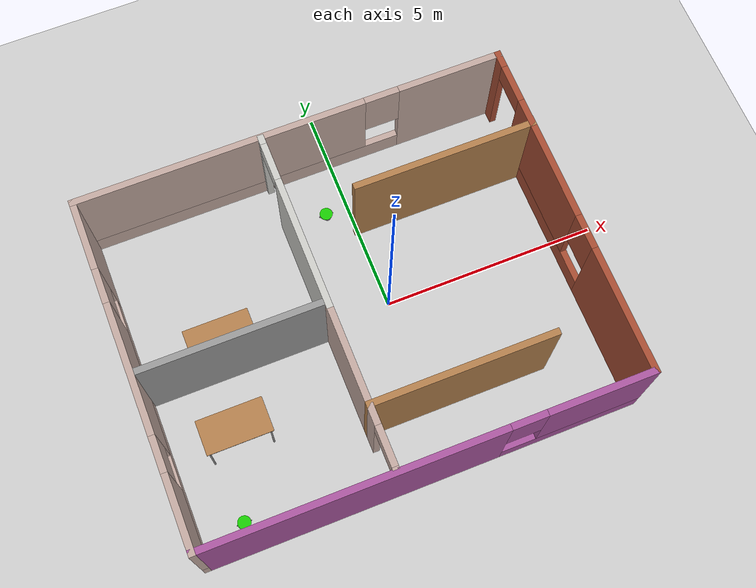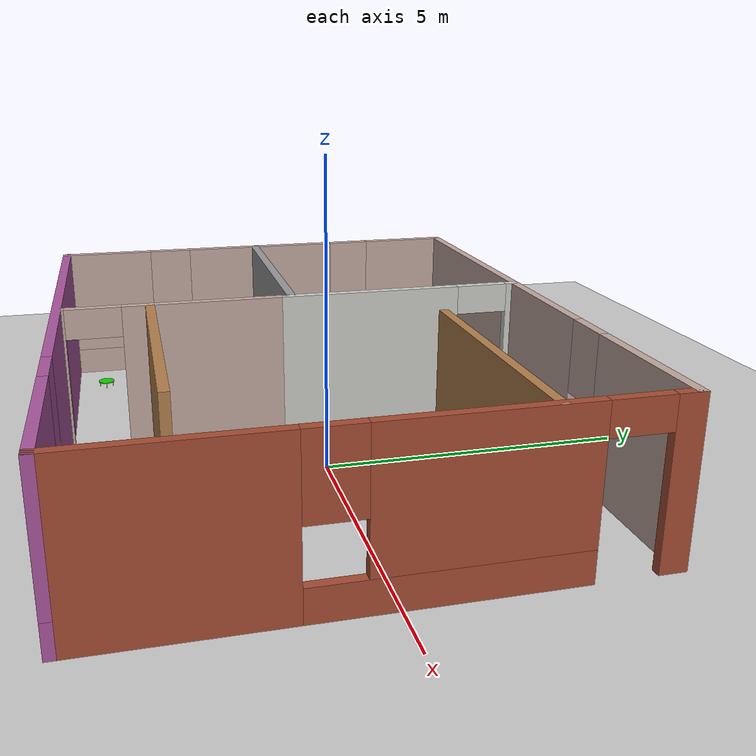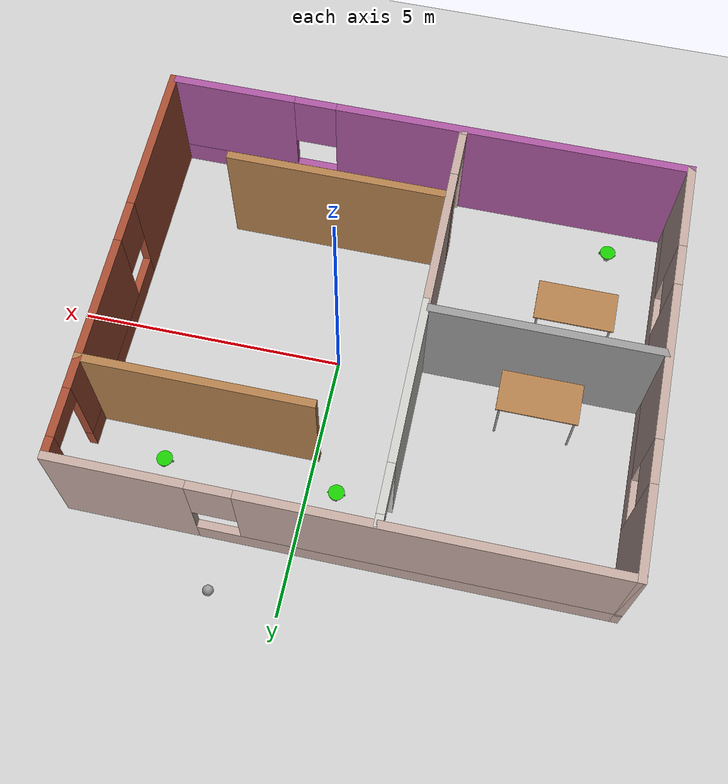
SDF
<sdf version="1.6">
 <world name="default">
  <plugin name="hello" filename="libhello.so"/>
  <light name="sun" type="directional">
   <pose>0 0 10 0 -0 0</pose>
   <diffuse>0.8 0.8 0.8 1</diffuse>
   <specular>0.2 0.2 0.2 1</specular>
   <attenuation>
    <range>1000</range>
    <constant>0.9</constant>
    <linear>0.01</linear>
    <quadratic>0.001</quadratic>
   </attenuation>
   <direction>-0.5 0.1 -0.9</direction>
  </light>
  <model name="ground_plane">
   <static>1</static>
   <link name="link">
    <collision name="collision">
     <geometry><plane><normal>0 0 1</normal><size>100 100</size></plane></geometry>
     <surface><friction><ode><mu>100</mu><mu2>50</mu2></ode></friction></surface>
    </collision>
    <visual name="visual">
     <cast_shadows>0</cast_shadows>
     <geometry><plane><normal>0 0 1</normal><size>100 100</size></plane></geometry>
     <material>
      <script><uri>file://media/materials/scripts/gazebo.material</uri><name>Gazebo/Grey</name></script>
     </material>
    </visual>
   </link>
  </model>
  <gravity>0 0 -9.8</gravity>
  <magnetic_field>6e-06 2.3e-05 -4.2e-05</magnetic_field>
  <atmosphere type="adiabatic"/>
  <physics name="default_physics" default="0" type="ode">
   <max_step_size>0.001</max_step_size>
   <real_time_factor>1</real_time_factor>
   <real_time_update_rate>1000</real_time_update_rate>
  </physics>
  <scene><ambient>0.4 0.4 0.4 1</ambient><background>0.7 0.7 0.7 1</background><shadows>1</shadows></scene>
  <spherical_coordinates>
   <surface_model>EARTH_WGS84</surface_model>
   <latitude_deg>0</latitude_deg>
   <longitude_deg>0</longitude_deg>
   <elevation>0</elevation>
   <heading_deg>0</heading_deg>
  </spherical_coordinates>
  <model name="my_building">
   <pose>-0.837268 -0.153391 0 0 0 -3.14159</pose>
   <link name="Wall_15">
    <collision name="Wall_15_Collision">
     <geometry><box><size>4.25 0.15 2.5</size></box></geometry>
     <pose>0 0 1.25 0 -0 0</pose>
    </collision>
    <visual name="Wall_15_Visual">
     <pose>0 0 1.25 0 -0 0</pose>
     <geometry><box><size>4.25 0.15 2.5</size></box></geometry>
     <material>
      <script><uri>file://media/materials/scripts/gazebo.material</uri><name>Gazebo/Grey</name></script>
      <ambient>1 1 1 1</ambient>
     </material>
     <meta><layer>0</layer></meta>
    </visual>
    <pose>2.84042 0.103421 0 0 -0 3.14159</pose>
   </link>
   <link name="Wall_21">
    <pose>0.686687 -1.84918 0 0 -0 1.5708</pose>
    <visual name="Wall_21_Visual_0">
     <pose>-2.0108 0 1.25 0 -0 0</pose>
     <geometry><box><size>0.228407 0.15 2.5</size></box></geometry>
     <material>
      <script><uri>file://media/materials/scripts/gazebo.material</uri><name>Gazebo/CeilingTiled</name></script>
      <ambient>0.760784 0.662745 0.627451 1</ambient>
     </material>
     <meta><layer>0</layer></meta>
    </visual>
    <collision name="Wall_21_Collision_0">
     <geometry><box><size>0.228407 0.15 2.5</size></box></geometry>
     <pose>-2.0108 0 1.25 0 -0 0</pose>
    </collision>
    <visual name="Wall_21_Visual_1">
     <pose>0.564203 0 1.25 0 -0 0</pose>
     <geometry><box><size>3.12159 0.15 2.5</size></box></geometry>
     <material>
      <script><uri>file://media/materials/scripts/gazebo.material</uri><name>Gazebo/CeilingTiled</name></script>
      <ambient>0.760784 0.662745 0.627451 1</ambient>
     </material>
     <meta><layer>0</layer></meta>
    </visual>
    <collision name="Wall_21_Collision_1">
     <geometry><box><size>3.12159 0.15 2.5</size></box></geometry>
     <pose>0.564203 0 1.25 0 -0 0</pose>
    </collision>
    <visual name="Wall_21_Visual_2">
     <pose>-1.44659 0 2.25 0 -0 0</pose>
     <geometry><box><size>0.9 0.15 0.5</size></box></geometry>
     <material>
      <script><uri>file://media/materials/scripts/gazebo.material</uri><name>Gazebo/CeilingTiled</name></script>
      <ambient>0.760784 0.662745 0.627451 1</ambient>
     </material>
     <meta><layer>0</layer></meta>
    </visual>
    <collision name="Wall_21_Collision_2">
     <geometry><box><size>0.9 0.15 0.5</size></box></geometry>
     <pose>-1.44659 0 2.25 0 -0 0</pose>
    </collision>
   </link>
   <link name="Wall_22">
    <pose>0.686687 2.00082 0 0 -0 1.5708</pose>
    <visual name="Wall_22_Visual_0">
     <pose>-0.482 0 1.25 0 -0 0</pose>
     <geometry><box><size>2.786 0.15 2.5</size></box></geometry>
     <material>
      <script><uri>file://media/materials/scripts/gazebo.material</uri><name>Gazebo/Grey</name></script>
      <ambient>0.760784 0.662745 0.627451 1</ambient>
     </material>
     <meta><layer>0</layer></meta>
    </visual>
    <collision name="Wall_22_Collision_0">
     <geometry><box><size>2.786 0.15 2.5</size></box></geometry>
     <pose>-0.482 0 1.25 0 -0 0</pose>
    </collision>
    <visual name="Wall_22_Visual_1">
     <pose>1.843 0 1.25 0 -0 0</pose>
     <geometry><box><size>0.064001 0.15 2.5</size></box></geometry>
     <material>
      <script><uri>file://media/materials/scripts/gazebo.material</uri><name>Gazebo/Grey</name></script>
      <ambient>0.760784 0.662745 0.627451 1</ambient>
     </material>
     <meta><layer>0</layer></meta>
    </visual>
    <collision name="Wall_22_Collision_1">
     <geometry><box><size>0.064001 0.15 2.5</size></box></geometry>
     <pose>1.843 0 1.25 0 -0 0</pose>
    </collision>
    <visual name="Wall_22_Visual_2">
     <pose>1.361 0 2.25 0 -0 0</pose>
     <geometry><box><size>0.9 0.15 0.5</size></box></geometry>
     <material>
      <script><uri>file://media/materials/scripts/gazebo.material</uri><name>Gazebo/Grey</name></script>
      <ambient>0.760784 0.662745 0.627451 1</ambient>
     </material>
     <meta><layer>0</layer></meta>
    </visual>
    <collision name="Wall_22_Collision_2">
     <geometry><box><size>0.9 0.15 0.5</size></box></geometry>
     <pose>1.361 0 2.25 0 -0 0</pose>
    </collision>
   </link>
   <link name="Wall_24">
    <collision name="Wall_24_Collision">
     <geometry><box><size>4.25 0.15 2.5</size></box></geometry>
     <pose>0 0 1.25 0 -0 0</pose>
    </collision>
    <visual name="Wall_24_Visual">
     <pose>0 0 1.25 0 -0 0</pose>
     <geometry><box><size>4.25 0.15 2.5</size></box></geometry>
     <material>
      <script><uri>file://media/materials/scripts/gazebo.material</uri><name>Gazebo/Wood</name></script>
      <ambient>1 1 1 1</ambient>
     </material>
     <meta><layer>0</layer></meta>
    </visual>
    <pose>-2.875 -2.08896 0 0 -0 0</pose>
   </link>
   <link name="Wall_26">
    <collision name="Wall_26_Collision">
     <geometry><box><size>4.25 0.15 2.5</size></box></geometry>
     <pose>0 0 1.25 0 -0 0</pose>
    </collision>
    <visual name="Wall_26_Visual">
     <pose>0 0 1.25 0 -0 0</pose>
     <geometry><box><size>4.25 0.15 2.5</size></box></geometry>
     <material>
      <script><uri>file://media/materials/scripts/gazebo.material</uri><name>Gazebo/Wood</name></script>
      <ambient>1 1 1 1</ambient>
     </material>
     <meta><layer>0</layer></meta>
    </visual>
    <pose>-1.36331 2.45671 0 0 -0 3.14159</pose>
   </link>
   <link name="Wall_3">
    <pose>-4.925 0 0 0 0 -1.5708</pose>
    <visual name="Wall_3_Visual_0">
     <pose>-2.5333 0 1.25 0 -0 0</pose>
     <geometry><box><size>2.9334 0.15 2.5</size></box></geometry>
     <material>
      <script><uri>file://media/materials/scripts/gazebo.material</uri><name>Gazebo/Bricks</name></script>
      <ambient>1 1 1 1</ambient>
     </material>
     <meta><layer>0</layer></meta>
    </visual>
    <collision name="Wall_3_Collision_0">
     <geometry><box><size>2.9334 0.15 2.5</size></box></geometry>
     <pose>-2.5333 0 1.25 0 -0 0</pose>
    </collision>
    <visual name="Wall_3_Visual_1">
     <pose>3.79243 0 1.25 0 -0 0</pose>
     <geometry><box><size>0.415136 0.15 2.5</size></box></geometry>
     <material>
      <script><uri>file://media/materials/scripts/gazebo.material</uri><name>Gazebo/Bricks</name></script>
      <ambient>1 1 1 1</ambient>
     </material>
     <meta><layer>0</layer></meta>
    </visual>
    <collision name="Wall_3_Collision_1">
     <geometry><box><size>0.415136 0.15 2.5</size></box></geometry>
     <pose>3.79243 0 1.25 0 -0 0</pose>
    </collision>
    <visual name="Wall_3_Visual_2">
     <pose>0.809131 0 0.25 0 -0 0</pose>
     <geometry><box><size>3.75147 0.15 0.5</size></box></geometry>
     <material>
      <script><uri>file://media/materials/scripts/gazebo.material</uri><name>Gazebo/Bricks</name></script>
      <ambient>1 1 1 1</ambient>
     </material>
     <meta><layer>0</layer></meta>
    </visual>
    <collision name="Wall_3_Collision_2">
     <geometry><box><size>3.75147 0.15 0.5</size></box></geometry>
     <pose>0.809131 0 0.25 0 -0 0</pose>
    </collision>
    <visual name="Wall_3_Visual_3">
     <pose>1.20913 0 1.5 0 -0 0</pose>
     <geometry><box><size>2.95146 0.15 2</size></box></geometry>
     <material>
      <script><uri>file://media/materials/scripts/gazebo.material</uri><name>Gazebo/Bricks</name></script>
      <ambient>1 1 1 1</ambient>
     </material>
     <meta><layer>0</layer></meta>
    </visual>
    <collision name="Wall_3_Collision_3">
     <geometry><box><size>2.95146 0.15 2</size></box></geometry>
     <pose>1.20913 0 1.5 0 -0 0</pose>
    </collision>
    <visual name="Wall_3_Visual_4">
     <pose>-0.666601 0 1.9 0 -0 0</pose>
     <geometry><box><size>0.8 0.15 1.2</size></box></geometry>
     <material>
      <script><uri>file://media/materials/scripts/gazebo.material</uri><name>Gazebo/Bricks</name></script>
      <ambient>1 1 1 1</ambient>
     </material>
     <meta><layer>0</layer></meta>
    </visual>
    <collision name="Wall_3_Collision_4">
     <geometry><box><size>0.8 0.15 1.2</size></box></geometry>
     <pose>-0.666601 0 1.9 0 -0 0</pose>
    </collision>
    <visual name="Wall_3_Visual_5">
     <pose>3.13486 0 2.25 0 -0 0</pose>
     <geometry><box><size>0.9 0.15 0.5</size></box></geometry>
     <material>
      <script><uri>file://media/materials/scripts/gazebo.material</uri><name>Gazebo/Bricks</name></script>
      <ambient>1 1 1 1</ambient>
     </material>
     <meta><layer>0</layer></meta>
    </visual>
    <collision name="Wall_3_Collision_5">
     <geometry><box><size>0.9 0.15 0.5</size></box></geometry>
     <pose>3.13486 0 2.25 0 -0 0</pose>
    </collision>
   </link>
   <link name="Wall_6">
    <pose>0 -3.925 0 0 -0 0</pose>
    <visual name="Wall_6_Visual_0">
     <pose>-3.76461 0 1.25 0 -0 0</pose>
     <geometry><box><size>2.47079 0.15 2.5</size></box></geometry>
     <material>
      <script><uri>file://media/materials/scripts/gazebo.material</uri><name>Gazebo/Grey</name></script>
      <ambient>0.760784 0.662745 0.627451 1</ambient>
     </material>
     <meta><layer>0</layer></meta>
    </visual>
    <collision name="Wall_6_Collision_0">
     <geometry><box><size>2.47079 0.15 2.5</size></box></geometry>
     <pose>-3.76461 0 1.25 0 -0 0</pose>
    </collision>
    <visual name="Wall_6_Visual_1">
     <pose>1.23539 0 0.25 0 -0 0</pose>
     <geometry><box><size>7.52921 0.15 0.5</size></box></geometry>
     <material>
      <script><uri>file://media/materials/scripts/gazebo.material</uri><name>Gazebo/Grey</name></script>
      <ambient>0.760784 0.662745 0.627451 1</ambient>
     </material>
     <meta><layer>0</layer></meta>
    </visual>
    <collision name="Wall_6_Collision_1">
     <geometry><box><size>7.52921 0.15 0.5</size></box></geometry>
     <pose>1.23539 0 0.25 0 -0 0</pose>
    </collision>
    <visual name="Wall_6_Visual_2">
     <pose>1.63539 0 1.5 0 -0 0</pose>
     <geometry><box><size>6.72921 0.15 2</size></box></geometry>
     <material>
      <script><uri>file://media/materials/scripts/gazebo.material</uri><name>Gazebo/Grey</name></script>
      <ambient>0.760784 0.662745 0.627451 1</ambient>
     </material>
     <meta><layer>0</layer></meta>
    </visual>
    <collision name="Wall_6_Collision_2">
     <geometry><box><size>6.72921 0.15 2</size></box></geometry>
     <pose>1.63539 0 1.5 0 -0 0</pose>
    </collision>
    <visual name="Wall_6_Visual_3">
     <pose>-2.12921 0 1.9 0 -0 0</pose>
     <geometry><box><size>0.8 0.15 1.2</size></box></geometry>
     <material>
      <script><uri>file://media/materials/scripts/gazebo.material</uri><name>Gazebo/Grey</name></script>
      <ambient>0.760784 0.662745 0.627451 1</ambient>
     </material>
     <meta><layer>0</layer></meta>
    </visual>
    <collision name="Wall_6_Collision_3">
     <geometry><box><size>0.8 0.15 1.2</size></box></geometry>
     <pose>-2.12921 0 1.9 0 -0 0</pose>
    </collision>
   </link>
   <link name="Wall_8">
    <pose>4.925 0 0 0 -0 1.5708</pose>
    <visual name="Wall_8_Visual_0">
     <pose>-3.15397 0 1.25 0 -0 0</pose>
     <geometry><box><size>1.69206 0.15 2.5</size></box></geometry>
     <material>
      <script><uri>file://media/materials/scripts/gazebo.material</uri><name>Gazebo/Grey</name></script>
      <ambient>0.760784 0.662745 0.627451 1</ambient>
     </material>
     <meta><layer>0</layer></meta>
    </visual>
    <collision name="Wall_8_Collision_0">
     <geometry><box><size>1.69206 0.15 2.5</size></box></geometry>
     <pose>-3.15397 0 1.25 0 -0 0</pose>
    </collision>
    <visual name="Wall_8_Visual_1">
     <pose>0.846032 0 0.25 0 -0 0</pose>
     <geometry><box><size>6.30794 0.15 0.5</size></box></geometry>
     <material>
      <script><uri>file://media/materials/scripts/gazebo.material</uri><name>Gazebo/Grey</name></script>
      <ambient>0.760784 0.662745 0.627451 1</ambient>
     </material>
     <meta><layer>0</layer></meta>
    </visual>
    <collision name="Wall_8_Collision_1">
     <geometry><box><size>6.30794 0.15 0.5</size></box></geometry>
     <pose>0.846032 0 0.25 0 -0 0</pose>
    </collision>
    <visual name="Wall_8_Visual_2">
     <pose>-0.01726 0 1.5 0 -0 0</pose>
     <geometry><box><size>2.98135 0.15 2</size></box></geometry>
     <material>
      <script><uri>file://media/materials/scripts/gazebo.material</uri><name>Gazebo/Grey</name></script>
      <ambient>0.760784 0.662745 0.627451 1</ambient>
     </material>
     <meta><layer>0</layer></meta>
    </visual>
    <collision name="Wall_8_Collision_2">
     <geometry><box><size>2.98135 0.15 2</size></box></geometry>
     <pose>-0.01726 0 1.5 0 -0 0</pose>
    </collision>
    <visual name="Wall_8_Visual_3">
     <pose>3.13671 0 1.5 0 -0 0</pose>
     <geometry><box><size>1.72658 0.15 2</size></box></geometry>
     <material>
      <script><uri>file://media/materials/scripts/gazebo.material</uri><name>Gazebo/Grey</name></script>
      <ambient>0.760784 0.662745 0.627451 1</ambient>
     </material>
     <meta><layer>0</layer></meta>
    </visual>
    <collision name="Wall_8_Collision_3">
     <geometry><box><size>1.72658 0.15 2</size></box></geometry>
     <pose>3.13671 0 1.5 0 -0 0</pose>
    </collision>
    <visual name="Wall_8_Visual_4">
     <pose>-1.90794 0 1.9 0 -0 0</pose>
     <geometry><box><size>0.8 0.15 1.2</size></box></geometry>
     <material>
      <script><uri>file://media/materials/scripts/gazebo.material</uri><name>Gazebo/Grey</name></script>
      <ambient>0.760784 0.662745 0.627451 1</ambient>
     </material>
     <meta><layer>0</layer></meta>
    </visual>
    <collision name="Wall_8_Collision_4">
     <geometry><box><size>0.8 0.15 1.2</size></box></geometry>
     <pose>-1.90794 0 1.9 0 -0 0</pose>
    </collision>
    <visual name="Wall_8_Visual_5">
     <pose>1.87342 0 1.9 0 -0 0</pose>
     <geometry><box><size>0.8 0.15 1.2</size></box></geometry>
     <material>
      <script><uri>file://media/materials/scripts/gazebo.material</uri><name>Gazebo/Grey</name></script>
      <ambient>0.760784 0.662745 0.627451 1</ambient>
     </material>
     <meta><layer>0</layer></meta>
    </visual>
    <collision name="Wall_8_Collision_5">
     <geometry><box><size>0.8 0.15 1.2</size></box></geometry>
     <pose>1.87342 0 1.9 0 -0 0</pose>
    </collision>
   </link>
   <link name="Wall_9">
    <pose>0 3.925 0 0 -0 3.14159</pose>
    <visual name="Wall_9_Visual_0">
     <pose>-1.62534 0 1.25 0 -0 0</pose>
     <geometry><box><size>6.74933 0.15 2.5</size></box></geometry>
     <material>
      <script><uri>file://media/materials/scripts/gazebo.material</uri><name>Gazebo/Grey</name></script>
      <ambient>0.666667 0.337255 0.623529 1</ambient>
     </material>
     <meta><layer>0</layer></meta>
    </visual>
    <collision name="Wall_9_Collision_0">
     <geometry><box><size>6.74933 0.15 2.5</size></box></geometry>
     <pose>-1.62534 0 1.25 0 -0 0</pose>
    </collision>
    <visual name="Wall_9_Visual_1">
     <pose>3.37466 0 0.25 0 -0 0</pose>
     <geometry><box><size>3.25067 0.15 0.5</size></box></geometry>
     <material>
      <script><uri>file://media/materials/scripts/gazebo.material</uri><name>Gazebo/Grey</name></script>
      <ambient>0.666667 0.337255 0.623529 1</ambient>
     </material>
     <meta><layer>0</layer></meta>
    </visual>
    <collision name="Wall_9_Collision_1">
     <geometry><box><size>3.25067 0.15 0.5</size></box></geometry>
     <pose>3.37466 0 0.25 0 -0 0</pose>
    </collision>
    <visual name="Wall_9_Visual_2">
     <pose>3.77466 0 1.5 0 -0 0</pose>
     <geometry><box><size>2.45067 0.15 2</size></box></geometry>
     <material>
      <script><uri>file://media/materials/scripts/gazebo.material</uri><name>Gazebo/Grey</name></script>
      <ambient>0.666667 0.337255 0.623529 1</ambient>
     </material>
     <meta><layer>0</layer></meta>
    </visual>
    <collision name="Wall_9_Collision_2">
     <geometry><box><size>2.45067 0.15 2</size></box></geometry>
     <pose>3.77466 0 1.5 0 -0 0</pose>
    </collision>
    <visual name="Wall_9_Visual_3">
     <pose>2.14933 0 1.9 0 -0 0</pose>
     <geometry><box><size>0.8 0.15 1.2</size></box></geometry>
     <material>
      <script><uri>file://media/materials/scripts/gazebo.material</uri><name>Gazebo/Grey</name></script>
      <ambient>0.666667 0.337255 0.623529 1</ambient>
     </material>
     <meta><layer>0</layer></meta>
    </visual>
    <collision name="Wall_9_Collision_3">
     <geometry><box><size>0.8 0.15 1.2</size></box></geometry>
     <pose>2.14933 0 1.9 0 -0 0</pose>
    </collision>
   </link>
   <static>1</static>
  </model>
  <model name="table">
   <static>1</static>
   <link name="link">
    <collision name="surface">
     <pose>0 0 1 0 -0 0</pose>
     <geometry><box><size>1.5 0.8 0.03</size></box></geometry>
     <surface><friction><ode><mu>0.6</mu><mu2>0.6</mu2></ode></friction></surface>
    </collision>
    <visual name="visual1">
     <pose>0 0 1 0 -0 0</pose>
     <geometry><box><size>1.5 0.8 0.03</size></box></geometry>
     <material>
      <script><uri>file://media/materials/scripts/gazebo.material</uri><name>Gazebo/Wood</name></script>
     </material>
    </visual>
    <collision name="front_left_leg">
     <pose>0.68 0.38 0.5 0 -0 0</pose>
     <geometry><cylinder><radius>0.02</radius><length>1</length></cylinder></geometry>
    </collision>
    <visual name="front_left_leg">
     <pose>0.68 0.38 0.5 0 -0 0</pose>
     <geometry><cylinder><radius>0.02</radius><length>1</length></cylinder></geometry>
     <material>
      <script><uri>file://media/materials/scripts/gazebo.material</uri><name>Gazebo/Grey</name></script>
     </material>
    </visual>
    <collision name="front_right_leg">
     <pose>0.68 -0.38 0.5 0 -0 0</pose>
     <geometry><cylinder><radius>0.02</radius><length>1</length></cylinder></geometry>
    </collision>
    <visual name="front_right_leg">
     <pose>0.68 -0.38 0.5 0 -0 0</pose>
     <geometry><cylinder><radius>0.02</radius><length>1</length></cylinder></geometry>
     <material>
      <script><uri>file://media/materials/scripts/gazebo.material</uri><name>Gazebo/Grey</name></script>
     </material>
    </visual>
    <collision name="back_right_leg">
     <pose>-0.68 -0.38 0.5 0 -0 0</pose>
     <geometry><cylinder><radius>0.02</radius><length>1</length></cylinder></geometry>
    </collision>
    <visual name="back_right_leg">
     <pose>-0.68 -0.38 0.5 0 -0 0</pose>
     <geometry><cylinder><radius>0.02</radius><length>1</length></cylinder></geometry>
     <material>
      <script><uri>file://media/materials/scripts/gazebo.material</uri><name>Gazebo/Grey</name></script>
     </material>
    </visual>
    <collision name="back_left_leg">
     <pose>-0.68 0.38 0.5 0 -0 0</pose>
     <geometry><cylinder><radius>0.02</radius><length>1</length></cylinder></geometry>
    </collision>
    <visual name="back_left_leg">
     <pose>-0.68 0.38 0.5 0 -0 0</pose>
     <geometry><cylinder><radius>0.02</radius><length>1</length></cylinder></geometry>
     <material>
      <script><uri>file://media/materials/scripts/gazebo.material</uri><name>Gazebo/Grey</name></script>
     </material>
    </visual>
   </link>
   <pose>-4.19604 -1.654 0 0 -0 0</pose>
  </model>
  <model name="table_0">
   <static>1</static>
   <link name="link">
    <collision name="surface">
     <pose>0 0 1 0 -0 0</pose>
     <geometry><box><size>1.5 0.8 0.03</size></box></geometry>
     <surface><friction><ode><mu>0.6</mu><mu2>0.6</mu2></ode></friction></surface>
    </collision>
    <visual name="visual1">
     <pose>0 0 1 0 -0 0</pose>
     <geometry><box><size>1.5 0.8 0.03</size></box></geometry>
     <material>
      <script><uri>file://media/materials/scripts/gazebo.material</uri><name>Gazebo/Wood</name></script>
     </material>
    </visual>
    <collision name="front_left_leg">
     <pose>0.68 0.38 0.5 0 -0 0</pose>
     <geometry><cylinder><radius>0.02</radius><length>1</length></cylinder></geometry>
    </collision>
    <visual name="front_left_leg">
     <pose>0.68 0.38 0.5 0 -0 0</pose>
     <geometry><cylinder><radius>0.02</radius><length>1</length></cylinder></geometry>
     <material>
      <script><uri>file://media/materials/scripts/gazebo.material</uri><name>Gazebo/Grey</name></script>
     </material>
    </visual>
    <collision name="front_right_leg">
     <pose>0.68 -0.38 0.5 0 -0 0</pose>
     <geometry><cylinder><radius>0.02</radius><length>1</length></cylinder></geometry>
    </collision>
    <visual name="front_right_leg">
     <pose>0.68 -0.38 0.5 0 -0 0</pose>
     <geometry><cylinder><radius>0.02</radius><length>1</length></cylinder></geometry>
     <material>
      <script><uri>file://media/materials/scripts/gazebo.material</uri><name>Gazebo/Grey</name></script>
     </material>
    </visual>
    <collision name="back_right_leg">
     <pose>-0.68 -0.38 0.5 0 -0 0</pose>
     <geometry><cylinder><radius>0.02</radius><length>1</length></cylinder></geometry>
    </collision>
    <visual name="back_right_leg">
     <pose>-0.68 -0.38 0.5 0 -0 0</pose>
     <geometry><cylinder><radius>0.02</radius><length>1</length></cylinder></geometry>
     <material>
      <script><uri>file://media/materials/scripts/gazebo.material</uri><name>Gazebo/Grey</name></script>
     </material>
    </visual>
    <collision name="back_left_leg">
     <pose>-0.68 0.38 0.5 0 -0 0</pose>
     <geometry><cylinder><radius>0.02</radius><length>1</length></cylinder></geometry>
    </collision>
    <visual name="back_left_leg">
     <pose>-0.68 0.38 0.5 0 -0 0</pose>
     <geometry><cylinder><radius>0.02</radius><length>1</length></cylinder></geometry>
     <material>
      <script><uri>file://media/materials/scripts/gazebo.material</uri><name>Gazebo/Grey</name></script>
     </material>
    </visual>
   </link>
   <pose>-3.81431 0.334745 0 0 -0 0</pose>
  </model>
  <model name="my_model">
   <link name="link_0">
    <pose>0 0 0.034444 0 -0 0</pose>
    <inertial>
     <mass>1</mass>
     <inertia><ixx>0.145833</ixx><ixy>0</ixy><ixz>0</ixz><iyy>0.145833</iyy><iyz>0</iyz><izz>0.125</izz></inertia>
    </inertial>
    <visual name="visual">
     <geometry><cylinder><radius>0.15</radius><length>0.02</length></cylinder></geometry>
     <material>
      <lighting>1</lighting>
      <script><uri>file://media/materials/scripts/gazebo.material</uri><name>Gazebo/Grey</name></script>
      <shader type="pixel"><normal_map>__default__</normal_map></shader>
      <ambient>0.01 0.5 0.01 1</ambient>
      <diffuse>0.1 0.8 0.01 1</diffuse>
      <specular>0.01 0.01 0.01 1</specular>
      <emissive>0 0 0 1</emissive>
     </material>
    </visual>
    <collision name="collision">
     <geometry><cylinder><radius>0.15</radius><length>0.02</length></cylinder></geometry>
     <surface>
      <friction>
       <ode><mu>1</mu><mu2>1</mu2><fdir1>0 0 0</fdir1><slip1>0</slip1><slip2>0</slip2></ode>
       <torsional>
        <coefficient>1</coefficient>
        <patch_radius>0</patch_radius>
        <surface_radius>0</surface_radius>
        <use_patch_radius>1</use_patch_radius>
        <ode><slip>0</slip></ode>
       </torsional>
      </friction>
      <bounce><restitution_coefficient>0</restitution_coefficient><threshold>1e+06</threshold></bounce>
      <contact>
       <collide_without_contact>0</collide_without_contact>
       <collide_without_contact_bitmask>1</collide_without_contact_bitmask>
       <collide_bitmask>1</collide_bitmask>
       <ode>
        <soft_cfm>0</soft_cfm>
        <soft_erp>0.2</soft_erp>
        <kp>1e+13</kp>
        <kd>1</kd>
        <max_vel>0.01</max_vel>
        <min_depth>0</min_depth>
       </ode>
       <bullet>
        <split_impulse>1</split_impulse>
        <split_impulse_penetration_threshold>-0.01</split_impulse_penetration_threshold>
        <soft_cfm>0</soft_cfm>
        <soft_erp>0.2</soft_erp>
        <kp>1e+13</kp>
        <kd>1</kd>
       </bullet>
      </contact>
     </surface>
    </collision>
   </link>
   <link name="link_1">
    <pose>0.12 0 -0.030556 1.5708 -0 0</pose>
    <inertial>
     <mass>1</mass>
     <inertia><ixx>0.145833</ixx><ixy>0</ixy><ixz>0</ixz><iyy>0.145833</iyy><iyz>0</iyz><izz>0.125</izz></inertia>
    </inertial>
    <visual name="visual">
     <geometry><cylinder><radius>0.05</radius><length>0.01</length></cylinder></geometry>
     <material>
      <lighting>1</lighting>
      <script><uri>file://media/materials/scripts/gazebo.material</uri><name>Gazebo/Grey</name></script>
      <shader type="pixel"><normal_map>__default__</normal_map></shader>
      <ambient>0.4 0.4 0.4 1</ambient>
      <diffuse>0.4 0.4 0.4 1</diffuse>
      <specular>0.01 0.01 0.01 1</specular>
      <emissive>0 0 0 1</emissive>
     </material>
    </visual>
    <collision name="collision">
     <geometry><cylinder><radius>0.05</radius><length>0.01</length></cylinder></geometry>
     <surface>
      <friction>
       <ode><mu>1</mu><mu2>1</mu2><fdir1>0 0 0</fdir1><slip1>0</slip1><slip2>0</slip2></ode>
       <torsional>
        <coefficient>1</coefficient>
        <patch_radius>0</patch_radius>
        <surface_radius>0</surface_radius>
        <use_patch_radius>1</use_patch_radius>
        <ode><slip>0</slip></ode>
       </torsional>
      </friction>
      <bounce><restitution_coefficient>0</restitution_coefficient><threshold>1e+06</threshold></bounce>
      <contact>
       <collide_without_contact>0</collide_without_contact>
       <collide_without_contact_bitmask>1</collide_without_contact_bitmask>
       <collide_bitmask>1</collide_bitmask>
       <ode>
        <soft_cfm>0</soft_cfm>
        <soft_erp>0.2</soft_erp>
        <kp>1e+13</kp>
        <kd>1</kd>
        <max_vel>0.01</max_vel>
        <min_depth>0</min_depth>
       </ode>
       <bullet>
        <split_impulse>1</split_impulse>
        <split_impulse_penetration_threshold>-0.01</split_impulse_penetration_threshold>
        <soft_cfm>0</soft_cfm>
        <soft_erp>0.2</soft_erp>
        <kp>1e+13</kp>
        <kd>1</kd>
       </bullet>
      </contact>
     </surface>
    </collision>
   </link>
   <link name="link_1_clone">
    <pose>0 0.12 -0.030556 1.5708 -0 0</pose>
    <inertial>
     <mass>1</mass>
     <inertia><ixx>0.145833</ixx><ixy>0</ixy><ixz>0</ixz><iyy>0.145833</iyy><iyz>0</iyz><izz>0.125</izz></inertia>
    </inertial>
    <visual name="visual">
     <geometry><cylinder><radius>0.05</radius><length>0.01</length></cylinder></geometry>
     <material>
      <lighting>1</lighting>
      <script><uri>file://media/materials/scripts/gazebo.material</uri><name>Gazebo/Grey</name></script>
      <shader type="pixel"><normal_map>__default__</normal_map></shader>
      <ambient>0.4 0.4 0.4 1</ambient>
      <diffuse>0.4 0.4 0.4 1</diffuse>
      <specular>0.01 0.01 0.01 1</specular>
      <emissive>0 0 0 1</emissive>
     </material>
    </visual>
    <collision name="collision">
     <geometry><cylinder><radius>0.05</radius><length>0.01</length></cylinder></geometry>
     <surface>
      <friction>
       <ode><mu>1</mu><mu2>1</mu2><fdir1>0 0 0</fdir1><slip1>0</slip1><slip2>0</slip2></ode>
       <torsional>
        <coefficient>1</coefficient>
        <patch_radius>0</patch_radius>
        <surface_radius>0</surface_radius>
        <use_patch_radius>1</use_patch_radius>
        <ode><slip>0</slip></ode>
       </torsional>
      </friction>
      <bounce><restitution_coefficient>0</restitution_coefficient><threshold>1e+06</threshold></bounce>
      <contact>
       <collide_without_contact>0</collide_without_contact>
       <collide_without_contact_bitmask>1</collide_without_contact_bitmask>
       <collide_bitmask>1</collide_bitmask>
       <ode>
        <soft_cfm>0</soft_cfm>
        <soft_erp>0.2</soft_erp>
        <kp>1e+13</kp>
        <kd>1</kd>
        <max_vel>0.01</max_vel>
        <min_depth>0</min_depth>
       </ode>
       <bullet>
        <split_impulse>1</split_impulse>
        <split_impulse_penetration_threshold>-0.01</split_impulse_penetration_threshold>
        <soft_cfm>0</soft_cfm>
        <soft_erp>0.2</soft_erp>
        <kp>1e+13</kp>
        <kd>1</kd>
       </bullet>
      </contact>
     </surface>
    </collision>
   </link>
   <link name="link_1_clone_0">
    <pose>0 -0.12 -0.030556 1.5708 -0 0</pose>
    <inertial>
     <mass>1</mass>
     <inertia><ixx>0.145833</ixx><ixy>0</ixy><ixz>0</ixz><iyy>0.145833</iyy><iyz>0</iyz><izz>0.125</izz></inertia>
    </inertial>
    <visual name="visual">
     <geometry><cylinder><radius>0.05</radius><length>0.01</length></cylinder></geometry>
     <material>
      <lighting>1</lighting>
      <script><uri>file://media/materials/scripts/gazebo.material</uri><name>Gazebo/Grey</name></script>
      <shader type="pixel"><normal_map>__default__</normal_map></shader>
      <ambient>0.4 0.4 0.4 1</ambient>
      <diffuse>0.4 0.4 0.4 1</diffuse>
      <specular>0.01 0.01 0.01 1</specular>
      <emissive>0 0 0 1</emissive>
     </material>
    </visual>
    <collision name="collision">
     <geometry><cylinder><radius>0.05</radius><length>0.01</length></cylinder></geometry>
     <surface>
      <friction>
       <ode><mu>1</mu><mu2>1</mu2><fdir1>0 0 0</fdir1><slip1>0</slip1><slip2>0</slip2></ode>
       <torsional>
        <coefficient>1</coefficient>
        <patch_radius>0</patch_radius>
        <surface_radius>0</surface_radius>
        <use_patch_radius>1</use_patch_radius>
        <ode><slip>0</slip></ode>
       </torsional>
      </friction>
      <bounce><restitution_coefficient>0</restitution_coefficient><threshold>1e+06</threshold></bounce>
      <contact>
       <collide_without_contact>0</collide_without_contact>
       <collide_without_contact_bitmask>1</collide_without_contact_bitmask>
       <collide_bitmask>1</collide_bitmask>
       <ode>
        <soft_cfm>0</soft_cfm>
        <soft_erp>0.2</soft_erp>
        <kp>1e+13</kp>
        <kd>1</kd>
        <max_vel>0.01</max_vel>
        <min_depth>0</min_depth>
       </ode>
       <bullet>
        <split_impulse>1</split_impulse>
        <split_impulse_penetration_threshold>-0.01</split_impulse_penetration_threshold>
        <soft_cfm>0</soft_cfm>
        <soft_erp>0.2</soft_erp>
        <kp>1e+13</kp>
        <kd>1</kd>
       </bullet>
      </contact>
     </surface>
    </collision>
   </link>
   <link name="link_1_clone_1">
    <pose>-0.12 0 -0.030556 1.5708 -0 0</pose>
    <inertial>
     <mass>1</mass>
     <inertia><ixx>0.145833</ixx><ixy>0</ixy><ixz>0</ixz><iyy>0.145833</iyy><iyz>0</iyz><izz>0.125</izz></inertia>
    </inertial>
    <visual name="visual">
     <geometry><cylinder><radius>0.05</radius><length>0.01</length></cylinder></geometry>
     <material>
      <lighting>1</lighting>
      <script><uri>file://media/materials/scripts/gazebo.material</uri><name>Gazebo/Grey</name></script>
      <shader type="pixel"><normal_map>__default__</normal_map></shader>
      <ambient>0.4 0.4 0.4 1</ambient>
      <diffuse>0.4 0.4 0.4 1</diffuse>
      <specular>0.01 0.01 0.01 1</specular>
      <emissive>0 0 0 1</emissive>
     </material>
    </visual>
    <collision name="collision">
     <geometry><cylinder><radius>0.05</radius><length>0.01</length></cylinder></geometry>
     <surface>
      <friction>
       <ode><mu>1</mu><mu2>1</mu2><fdir1>0 0 0</fdir1><slip1>0</slip1><slip2>0</slip2></ode>
       <torsional>
        <coefficient>1</coefficient>
        <patch_radius>0</patch_radius>
        <surface_radius>0</surface_radius>
        <use_patch_radius>1</use_patch_radius>
        <ode><slip>0</slip></ode>
       </torsional>
      </friction>
      <bounce><restitution_coefficient>0</restitution_coefficient><threshold>1e+06</threshold></bounce>
      <contact>
       <collide_without_contact>0</collide_without_contact>
       <collide_without_contact_bitmask>1</collide_without_contact_bitmask>
       <collide_bitmask>1</collide_bitmask>
       <ode>
        <soft_cfm>0</soft_cfm>
        <soft_erp>0.2</soft_erp>
        <kp>1e+13</kp>
        <kd>1</kd>
        <max_vel>0.01</max_vel>
        <min_depth>0</min_depth>
       </ode>
       <bullet>
        <split_impulse>1</split_impulse>
        <split_impulse_penetration_threshold>-0.01</split_impulse_penetration_threshold>
        <soft_cfm>0</soft_cfm>
        <soft_erp>0.2</soft_erp>
        <kp>1e+13</kp>
        <kd>1</kd>
       </bullet>
      </contact>
     </surface>
    </collision>
   </link>
   <link name="link_3">
    <pose>-0.12 0 0.021944 0 -0 0</pose>
    <inertial>
     <mass>1</mass>
     <inertia><ixx>0.145833</ixx><ixy>0</ixy><ixz>0</ixz><iyy>0.145833</iyy><iyz>0</iyz><izz>0.125</izz></inertia>
    </inertial>
    <visual name="visual">
     <geometry><cylinder><radius>0.03</radius><length>0.005</length></cylinder></geometry>
     <material>
      <lighting>1</lighting>
      <script><uri>file://media/materials/scripts/gazebo.material</uri><name>Gazebo/Grey</name></script>
      <shader type="pixel"><normal_map>__default__</normal_map></shader>
      <ambient>0.3 0.3 0.7 1</ambient>
      <diffuse>0.7 0.7 0.9 1</diffuse>
      <specular>0.01 0.01 0.01 1</specular>
      <emissive>0 0 0 1</emissive>
     </material>
    </visual>
    <collision name="collision">
     <geometry><cylinder><radius>0.03</radius><length>0.005</length></cylinder></geometry>
     <surface>
      <friction>
       <ode><mu>1</mu><mu2>1</mu2><fdir1>0 0 0</fdir1><slip1>0</slip1><slip2>0</slip2></ode>
       <torsional>
        <coefficient>1</coefficient>
        <patch_radius>0</patch_radius>
        <surface_radius>0</surface_radius>
        <use_patch_radius>1</use_patch_radius>
        <ode><slip>0</slip></ode>
       </torsional>
      </friction>
      <bounce><restitution_coefficient>0</restitution_coefficient><threshold>1e+06</threshold></bounce>
      <contact>
       <collide_without_contact>0</collide_without_contact>
       <collide_without_contact_bitmask>1</collide_without_contact_bitmask>
       <collide_bitmask>1</collide_bitmask>
       <ode>
        <soft_cfm>0</soft_cfm>
        <soft_erp>0.2</soft_erp>
        <kp>1e+13</kp>
        <kd>1</kd>
        <max_vel>0.01</max_vel>
        <min_depth>0</min_depth>
       </ode>
       <bullet>
        <split_impulse>1</split_impulse>
        <split_impulse_penetration_threshold>-0.01</split_impulse_penetration_threshold>
        <soft_cfm>0</soft_cfm>
        <soft_erp>0.2</soft_erp>
        <kp>1e+13</kp>
        <kd>1</kd>
       </bullet>
      </contact>
     </surface>
    </collision>
   </link>
   <link name="link_3_clone">
    <pose>0.12 0 0.021944 0 -0 0</pose>
    <inertial>
     <mass>1</mass>
     <inertia><ixx>0.145833</ixx><ixy>0</ixy><ixz>0</ixz><iyy>0.145833</iyy><iyz>0</iyz><izz>0.125</izz></inertia>
    </inertial>
    <visual name="visual">
     <geometry><cylinder><radius>0.03</radius><length>0.005</length></cylinder></geometry>
     <material>
      <lighting>1</lighting>
      <script><uri>file://media/materials/scripts/gazebo.material</uri><name>Gazebo/Grey</name></script>
      <shader type="pixel"><normal_map>__default__</normal_map></shader>
      <ambient>0.3 0.3 0.7 1</ambient>
      <diffuse>0.7 0.7 0.9 1</diffuse>
      <specular>0.01 0.01 0.01 1</specular>
      <emissive>0 0 0 1</emissive>
     </material>
    </visual>
    <collision name="collision">
     <geometry><cylinder><radius>0.03</radius><length>0.005</length></cylinder></geometry>
     <surface>
      <friction>
       <ode><mu>1</mu><mu2>1</mu2><fdir1>0 0 0</fdir1><slip1>0</slip1><slip2>0</slip2></ode>
       <torsional>
        <coefficient>1</coefficient>
        <patch_radius>0</patch_radius>
        <surface_radius>0</surface_radius>
        <use_patch_radius>1</use_patch_radius>
        <ode><slip>0</slip></ode>
       </torsional>
      </friction>
      <bounce><restitution_coefficient>0</restitution_coefficient><threshold>1e+06</threshold></bounce>
      <contact>
       <collide_without_contact>0</collide_without_contact>
       <collide_without_contact_bitmask>1</collide_without_contact_bitmask>
       <collide_bitmask>1</collide_bitmask>
       <ode>
        <soft_cfm>0</soft_cfm>
        <soft_erp>0.2</soft_erp>
        <kp>1e+13</kp>
        <kd>1</kd>
        <max_vel>0.01</max_vel>
        <min_depth>0</min_depth>
       </ode>
       <bullet>
        <split_impulse>1</split_impulse>
        <split_impulse_penetration_threshold>-0.01</split_impulse_penetration_threshold>
        <soft_cfm>0</soft_cfm>
        <soft_erp>0.2</soft_erp>
        <kp>1e+13</kp>
        <kd>1</kd>
       </bullet>
      </contact>
     </surface>
    </collision>
   </link>
   <link name="link_3_clone_0">
    <pose>0 0.12 0.021944 0 -0 0</pose>
    <inertial>
     <mass>1</mass>
     <inertia><ixx>0.145833</ixx><ixy>0</ixy><ixz>0</ixz><iyy>0.145833</iyy><iyz>0</iyz><izz>0.125</izz></inertia>
    </inertial>
    <visual name="visual">
     <geometry><cylinder><radius>0.03</radius><length>0.005</length></cylinder></geometry>
     <material>
      <lighting>1</lighting>
      <script><uri>file://media/materials/scripts/gazebo.material</uri><name>Gazebo/Grey</name></script>
      <shader type="pixel"><normal_map>__default__</normal_map></shader>
      <ambient>0.3 0.3 0.7 1</ambient>
      <diffuse>0.7 0.7 0.9 1</diffuse>
      <specular>0.01 0.01 0.01 1</specular>
      <emissive>0 0 0 1</emissive>
     </material>
    </visual>
    <collision name="collision">
     <geometry><cylinder><radius>0.03</radius><length>0.005</length></cylinder></geometry>
     <surface>
      <friction>
       <ode><mu>1</mu><mu2>1</mu2><fdir1>0 0 0</fdir1><slip1>0</slip1><slip2>0</slip2></ode>
       <torsional>
        <coefficient>1</coefficient>
        <patch_radius>0</patch_radius>
        <surface_radius>0</surface_radius>
        <use_patch_radius>1</use_patch_radius>
        <ode><slip>0</slip></ode>
       </torsional>
      </friction>
      <bounce><restitution_coefficient>0</restitution_coefficient><threshold>1e+06</threshold></bounce>
      <contact>
       <collide_without_contact>0</collide_without_contact>
       <collide_without_contact_bitmask>1</collide_without_contact_bitmask>
       <collide_bitmask>1</collide_bitmask>
       <ode>
        <soft_cfm>0</soft_cfm>
        <soft_erp>0.2</soft_erp>
        <kp>1e+13</kp>
        <kd>1</kd>
        <max_vel>0.01</max_vel>
        <min_depth>0</min_depth>
       </ode>
       <bullet>
        <split_impulse>1</split_impulse>
        <split_impulse_penetration_threshold>-0.01</split_impulse_penetration_threshold>
        <soft_cfm>0</soft_cfm>
        <soft_erp>0.2</soft_erp>
        <kp>1e+13</kp>
        <kd>1</kd>
       </bullet>
      </contact>
     </surface>
    </collision>
   </link>
   <link name="link_3_clone_1">
    <pose>0 -0.12 0.021944 0 -0 0</pose>
    <inertial>
     <mass>1</mass>
     <inertia><ixx>0.145833</ixx><ixy>0</ixy><ixz>0</ixz><iyy>0.145833</iyy><iyz>0</iyz><izz>0.125</izz></inertia>
    </inertial>
    <visual name="visual">
     <geometry><cylinder><radius>0.03</radius><length>0.005</length></cylinder></geometry>
     <material>
      <lighting>1</lighting>
      <script><uri>file://media/materials/scripts/gazebo.material</uri><name>Gazebo/Grey</name></script>
      <shader type="pixel"><normal_map>__default__</normal_map></shader>
      <ambient>0.3 0.3 0.7 1</ambient>
      <diffuse>0.7 0.7 0.9 1</diffuse>
      <specular>0.01 0.01 0.01 1</specular>
      <emissive>0 0 0 1</emissive>
     </material>
    </visual>
    <collision name="collision">
     <geometry><cylinder><radius>0.03</radius><length>0.005</length></cylinder></geometry>
     <surface>
      <friction>
       <ode><mu>1</mu><mu2>1</mu2><fdir1>0 0 0</fdir1><slip1>0</slip1><slip2>0</slip2></ode>
       <torsional>
        <coefficient>1</coefficient>
        <patch_radius>0</patch_radius>
        <surface_radius>0</surface_radius>
        <use_patch_radius>1</use_patch_radius>
        <ode><slip>0</slip></ode>
       </torsional>
      </friction>
      <bounce><restitution_coefficient>0</restitution_coefficient><threshold>1e+06</threshold></bounce>
      <contact>
       <collide_without_contact>0</collide_without_contact>
       <collide_without_contact_bitmask>1</collide_without_contact_bitmask>
       <collide_bitmask>1</collide_bitmask>
       <ode>
        <soft_cfm>0</soft_cfm>
        <soft_erp>0.2</soft_erp>
        <kp>1e+13</kp>
        <kd>1</kd>
        <max_vel>0.01</max_vel>
        <min_depth>0</min_depth>
       </ode>
       <bullet>
        <split_impulse>1</split_impulse>
        <split_impulse_penetration_threshold>-0.01</split_impulse_penetration_threshold>
        <soft_cfm>0</soft_cfm>
        <soft_erp>0.2</soft_erp>
        <kp>1e+13</kp>
        <kd>1</kd>
       </bullet>
      </contact>
     </surface>
    </collision>
   </link>
   <joint name="link_0_JOINT_0" type="revolute">
    <parent>link_0</parent>
    <child>link_3_clone</child>
    <axis>
     <xyz>0 0 1</xyz>
     <use_parent_model_frame>0</use_parent_model_frame>
     <limit>
      <lower>-1.79769e+308</lower>
      <upper>1.79769e+308</upper>
      <effort>-1</effort>
      <velocity>-1</velocity>
     </limit>
     <dynamics>
      <spring_reference>0</spring_reference>
      <spring_stiffness>0</spring_stiffness>
      <damping>0</damping>
      <friction>0</friction>
     </dynamics>
    </axis>
    <physics>
     <ode><limit><cfm>0</cfm><erp>0.2</erp></limit><suspension><cfm>0</cfm><erp>0.2</erp></suspension></ode>
    </physics>
   </joint>
   <joint name="link_0_JOINT_1" type="revolute">
    <parent>link_0</parent>
    <child>link_3_clone_0</child>
    <axis>
     <xyz>0 0 1</xyz>
     <use_parent_model_frame>0</use_parent_model_frame>
     <limit>
      <lower>-1.79769e+308</lower>
      <upper>1.79769e+308</upper>
      <effort>-1</effort>
      <velocity>-1</velocity>
     </limit>
     <dynamics>
      <spring_reference>0</spring_reference>
      <spring_stiffness>0</spring_stiffness>
      <damping>0</damping>
      <friction>0</friction>
     </dynamics>
    </axis>
    <physics>
     <ode><limit><cfm>0</cfm><erp>0.2</erp></limit><suspension><cfm>0</cfm><erp>0.2</erp></suspension></ode>
    </physics>
   </joint>
   <joint name="link_0_JOINT_2" type="revolute">
    <parent>link_0</parent>
    <child>link_3_clone_1</child>
    <axis>
     <xyz>0 0 1</xyz>
     <use_parent_model_frame>0</use_parent_model_frame>
     <limit>
      <lower>-1.79769e+308</lower>
      <upper>1.79769e+308</upper>
      <effort>-1</effort>
      <velocity>-1</velocity>
     </limit>
     <dynamics>
      <spring_reference>0</spring_reference>
      <spring_stiffness>0</spring_stiffness>
      <damping>0</damping>
      <friction>0</friction>
     </dynamics>
    </axis>
    <physics>
     <ode><limit><cfm>0</cfm><erp>0.2</erp></limit><suspension><cfm>0</cfm><erp>0.2</erp></suspension></ode>
    </physics>
   </joint>
   <joint name="link_0_JOINT_3" type="revolute">
    <parent>link_0</parent>
    <child>link_3</child>
    <axis>
     <xyz>0 0 1</xyz>
     <use_parent_model_frame>0</use_parent_model_frame>
     <limit>
      <lower>-1.79769e+308</lower>
      <upper>1.79769e+308</upper>
      <effort>-1</effort>
      <velocity>-1</velocity>
     </limit>
     <dynamics>
      <spring_reference>0</spring_reference>
      <spring_stiffness>0</spring_stiffness>
      <damping>0</damping>
      <friction>0</friction>
     </dynamics>
    </axis>
    <physics>
     <ode><limit><cfm>0</cfm><erp>0.2</erp></limit><suspension><cfm>0</cfm><erp>0.2</erp></suspension></ode>
    </physics>
   </joint>
   <joint name="link_3_JOINT_4" type="revolute">
    <parent>link_3</parent>
    <child>link_1_clone_1</child>
    <axis>
     <xyz>1 0 0</xyz>
     <use_parent_model_frame>0</use_parent_model_frame>
     <limit>
      <lower>-1.79769e+308</lower>
      <upper>1.79769e+308</upper>
      <effort>-1</effort>
      <velocity>-1</velocity>
     </limit>
     <dynamics>
      <spring_reference>0</spring_reference>
      <spring_stiffness>0</spring_stiffness>
      <damping>0</damping>
      <friction>0</friction>
     </dynamics>
    </axis>
    <physics>
     <ode><limit><cfm>0</cfm><erp>0.2</erp></limit><suspension><cfm>0</cfm><erp>0.2</erp></suspension></ode>
    </physics>
   </joint>
   <joint name="link_3_clone_0_JOINT_6" type="revolute">
    <parent>link_3_clone_0</parent>
    <child>link_1_clone</child>
    <axis>
     <xyz>1 0 0</xyz>
     <use_parent_model_frame>0</use_parent_model_frame>
     <limit>
      <lower>-1.79769e+308</lower>
      <upper>1.79769e+308</upper>
      <effort>-1</effort>
      <velocity>-1</velocity>
     </limit>
     <dynamics>
      <spring_reference>0</spring_reference>
      <spring_stiffness>0</spring_stiffness>
      <damping>0</damping>
      <friction>0</friction>
     </dynamics>
    </axis>
    <physics>
     <ode><limit><cfm>0</cfm><erp>0.2</erp></limit><suspension><cfm>0</cfm><erp>0.2</erp></suspension></ode>
    </physics>
   </joint>
   <joint name="link_3_clone_1_JOINT_7" type="revolute">
    <parent>link_3_clone_1</parent>
    <child>link_1_clone_0</child>
    <axis>
     <xyz>1 0 0</xyz>
     <use_parent_model_frame>0</use_parent_model_frame>
     <limit>
      <lower>-1.79769e+308</lower>
      <upper>1.79769e+308</upper>
      <effort>-1</effort>
      <velocity>-1</velocity>
     </limit>
     <dynamics>
      <spring_reference>0</spring_reference>
      <spring_stiffness>0</spring_stiffness>
      <damping>0</damping>
      <friction>0</friction>
     </dynamics>
    </axis>
    <physics>
     <ode><limit><cfm>0</cfm><erp>0.2</erp></limit><suspension><cfm>0</cfm><erp>0.2</erp></suspension></ode>
    </physics>
   </joint>
   <joint name="link_3_clone_JOINT_5" type="revolute">
    <parent>link_3_clone</parent>
    <child>link_1</child>
    <axis>
     <xyz>1 0 0</xyz>
     <use_parent_model_frame>0</use_parent_model_frame>
     <limit>
      <lower>-1.79769e+308</lower>
      <upper>1.79769e+308</upper>
      <effort>-1</effort>
      <velocity>-1</velocity>
     </limit>
     <dynamics>
      <spring_reference>0</spring_reference>
      <spring_stiffness>0</spring_stiffness>
      <damping>0</damping>
      <friction>0</friction>
     </dynamics>
    </axis>
    <physics>
     <ode><limit><cfm>0</cfm><erp>0.2</erp></limit><suspension><cfm>0</cfm><erp>0.2</erp></suspension></ode>
    </physics>
   </joint>
   <static>0</static>
   <pose>2.69535 2.58657 0.080556 -4e-06 2e-06 -0.000326</pose>
  </model>
  <model name="my_model_0">
   <link name="link_0">
    <pose>0 0 0.034444 0 -0 0</pose>
    <inertial>
     <mass>1</mass>
     <inertia><ixx>0.145833</ixx><ixy>0</ixy><ixz>0</ixz><iyy>0.145833</iyy><iyz>0</iyz><izz>0.125</izz></inertia>
    </inertial>
    <visual name="visual">
     <geometry><cylinder><radius>0.15</radius><length>0.02</length></cylinder></geometry>
     <material>
      <lighting>1</lighting>
      <script><uri>file://media/materials/scripts/gazebo.material</uri><name>Gazebo/Grey</name></script>
      <shader type="pixel"><normal_map>__default__</normal_map></shader>
      <ambient>0.01 0.5 0.01 1</ambient>
      <diffuse>0.1 0.8 0.01 1</diffuse>
      <specular>0.01 0.01 0.01 1</specular>
      <emissive>0 0 0 1</emissive>
     </material>
    </visual>
    <collision name="collision">
     <geometry><cylinder><radius>0.15</radius><length>0.02</length></cylinder></geometry>
     <surface>
      <friction>
       <ode><mu>1</mu><mu2>1</mu2><fdir1>0 0 0</fdir1><slip1>0</slip1><slip2>0</slip2></ode>
       <torsional>
        <coefficient>1</coefficient>
        <patch_radius>0</patch_radius>
        <surface_radius>0</surface_radius>
        <use_patch_radius>1</use_patch_radius>
        <ode><slip>0</slip></ode>
       </torsional>
      </friction>
      <bounce><restitution_coefficient>0</restitution_coefficient><threshold>1e+06</threshold></bounce>
      <contact>
       <collide_without_contact>0</collide_without_contact>
       <collide_without_contact_bitmask>1</collide_without_contact_bitmask>
       <collide_bitmask>1</collide_bitmask>
       <ode>
        <soft_cfm>0</soft_cfm>
        <soft_erp>0.2</soft_erp>
        <kp>1e+13</kp>
        <kd>1</kd>
        <max_vel>0.01</max_vel>
        <min_depth>0</min_depth>
       </ode>
       <bullet>
        <split_impulse>1</split_impulse>
        <split_impulse_penetration_threshold>-0.01</split_impulse_penetration_threshold>
        <soft_cfm>0</soft_cfm>
        <soft_erp>0.2</soft_erp>
        <kp>1e+13</kp>
        <kd>1</kd>
       </bullet>
      </contact>
     </surface>
    </collision>
   </link>
   <link name="link_1">
    <pose>0.12 0 -0.030556 1.5708 -0 0</pose>
    <inertial>
     <mass>1</mass>
     <inertia><ixx>0.145833</ixx><ixy>0</ixy><ixz>0</ixz><iyy>0.145833</iyy><iyz>0</iyz><izz>0.125</izz></inertia>
    </inertial>
    <visual name="visual">
     <geometry><cylinder><radius>0.05</radius><length>0.01</length></cylinder></geometry>
     <material>
      <lighting>1</lighting>
      <script><uri>file://media/materials/scripts/gazebo.material</uri><name>Gazebo/Grey</name></script>
      <shader type="pixel"><normal_map>__default__</normal_map></shader>
      <ambient>0.4 0.4 0.4 1</ambient>
      <diffuse>0.4 0.4 0.4 1</diffuse>
      <specular>0.01 0.01 0.01 1</specular>
      <emissive>0 0 0 1</emissive>
     </material>
    </visual>
    <collision name="collision">
     <geometry><cylinder><radius>0.05</radius><length>0.01</length></cylinder></geometry>
     <surface>
      <friction>
       <ode><mu>1</mu><mu2>1</mu2><fdir1>0 0 0</fdir1><slip1>0</slip1><slip2>0</slip2></ode>
       <torsional>
        <coefficient>1</coefficient>
        <patch_radius>0</patch_radius>
        <surface_radius>0</surface_radius>
        <use_patch_radius>1</use_patch_radius>
        <ode><slip>0</slip></ode>
       </torsional>
      </friction>
      <bounce><restitution_coefficient>0</restitution_coefficient><threshold>1e+06</threshold></bounce>
      <contact>
       <collide_without_contact>0</collide_without_contact>
       <collide_without_contact_bitmask>1</collide_without_contact_bitmask>
       <collide_bitmask>1</collide_bitmask>
       <ode>
        <soft_cfm>0</soft_cfm>
        <soft_erp>0.2</soft_erp>
        <kp>1e+13</kp>
        <kd>1</kd>
        <max_vel>0.01</max_vel>
        <min_depth>0</min_depth>
       </ode>
       <bullet>
        <split_impulse>1</split_impulse>
        <split_impulse_penetration_threshold>-0.01</split_impulse_penetration_threshold>
        <soft_cfm>0</soft_cfm>
        <soft_erp>0.2</soft_erp>
        <kp>1e+13</kp>
        <kd>1</kd>
       </bullet>
      </contact>
     </surface>
    </collision>
   </link>
   <link name="link_1_clone">
    <pose>0 0.12 -0.030556 1.5708 -0 0</pose>
    <inertial>
     <mass>1</mass>
     <inertia><ixx>0.145833</ixx><ixy>0</ixy><ixz>0</ixz><iyy>0.145833</iyy><iyz>0</iyz><izz>0.125</izz></inertia>
    </inertial>
    <visual name="visual">
     <geometry><cylinder><radius>0.05</radius><length>0.01</length></cylinder></geometry>
     <material>
      <lighting>1</lighting>
      <script><uri>file://media/materials/scripts/gazebo.material</uri><name>Gazebo/Grey</name></script>
      <shader type="pixel"><normal_map>__default__</normal_map></shader>
      <ambient>0.4 0.4 0.4 1</ambient>
      <diffuse>0.4 0.4 0.4 1</diffuse>
      <specular>0.01 0.01 0.01 1</specular>
      <emissive>0 0 0 1</emissive>
     </material>
    </visual>
    <collision name="collision">
     <geometry><cylinder><radius>0.05</radius><length>0.01</length></cylinder></geometry>
     <surface>
      <friction>
       <ode><mu>1</mu><mu2>1</mu2><fdir1>0 0 0</fdir1><slip1>0</slip1><slip2>0</slip2></ode>
       <torsional>
        <coefficient>1</coefficient>
        <patch_radius>0</patch_radius>
        <surface_radius>0</surface_radius>
        <use_patch_radius>1</use_patch_radius>
        <ode><slip>0</slip></ode>
       </torsional>
      </friction>
      <bounce><restitution_coefficient>0</restitution_coefficient><threshold>1e+06</threshold></bounce>
      <contact>
       <collide_without_contact>0</collide_without_contact>
       <collide_without_contact_bitmask>1</collide_without_contact_bitmask>
       <collide_bitmask>1</collide_bitmask>
       <ode>
        <soft_cfm>0</soft_cfm>
        <soft_erp>0.2</soft_erp>
        <kp>1e+13</kp>
        <kd>1</kd>
        <max_vel>0.01</max_vel>
        <min_depth>0</min_depth>
       </ode>
       <bullet>
        <split_impulse>1</split_impulse>
        <split_impulse_penetration_threshold>-0.01</split_impulse_penetration_threshold>
        <soft_cfm>0</soft_cfm>
        <soft_erp>0.2</soft_erp>
        <kp>1e+13</kp>
        <kd>1</kd>
       </bullet>
      </contact>
     </surface>
    </collision>
   </link>
   <link name="link_1_clone_0">
    <pose>0 -0.12 -0.030556 1.5708 -0 0</pose>
    <inertial>
     <mass>1</mass>
     <inertia><ixx>0.145833</ixx><ixy>0</ixy><ixz>0</ixz><iyy>0.145833</iyy><iyz>0</iyz><izz>0.125</izz></inertia>
    </inertial>
    <visual name="visual">
     <geometry><cylinder><radius>0.05</radius><length>0.01</length></cylinder></geometry>
     <material>
      <lighting>1</lighting>
      <script><uri>file://media/materials/scripts/gazebo.material</uri><name>Gazebo/Grey</name></script>
      <shader type="pixel"><normal_map>__default__</normal_map></shader>
      <ambient>0.4 0.4 0.4 1</ambient>
      <diffuse>0.4 0.4 0.4 1</diffuse>
      <specular>0.01 0.01 0.01 1</specular>
      <emissive>0 0 0 1</emissive>
     </material>
    </visual>
    <collision name="collision">
     <geometry><cylinder><radius>0.05</radius><length>0.01</length></cylinder></geometry>
     <surface>
      <friction>
       <ode><mu>1</mu><mu2>1</mu2><fdir1>0 0 0</fdir1><slip1>0</slip1><slip2>0</slip2></ode>
       <torsional>
        <coefficient>1</coefficient>
        <patch_radius>0</patch_radius>
        <surface_radius>0</surface_radius>
        <use_patch_radius>1</use_patch_radius>
        <ode><slip>0</slip></ode>
       </torsional>
      </friction>
      <bounce><restitution_coefficient>0</restitution_coefficient><threshold>1e+06</threshold></bounce>
      <contact>
       <collide_without_contact>0</collide_without_contact>
       <collide_without_contact_bitmask>1</collide_without_contact_bitmask>
       <collide_bitmask>1</collide_bitmask>
       <ode>
        <soft_cfm>0</soft_cfm>
        <soft_erp>0.2</soft_erp>
        <kp>1e+13</kp>
        <kd>1</kd>
        <max_vel>0.01</max_vel>
        <min_depth>0</min_depth>
       </ode>
       <bullet>
        <split_impulse>1</split_impulse>
        <split_impulse_penetration_threshold>-0.01</split_impulse_penetration_threshold>
        <soft_cfm>0</soft_cfm>
        <soft_erp>0.2</soft_erp>
        <kp>1e+13</kp>
        <kd>1</kd>
       </bullet>
      </contact>
     </surface>
    </collision>
   </link>
   <link name="link_1_clone_1">
    <pose>-0.12 0 -0.030556 1.5708 -0 0</pose>
    <inertial>
     <mass>1</mass>
     <inertia><ixx>0.145833</ixx><ixy>0</ixy><ixz>0</ixz><iyy>0.145833</iyy><iyz>0</iyz><izz>0.125</izz></inertia>
    </inertial>
    <visual name="visual">
     <geometry><cylinder><radius>0.05</radius><length>0.01</length></cylinder></geometry>
     <material>
      <lighting>1</lighting>
      <script><uri>file://media/materials/scripts/gazebo.material</uri><name>Gazebo/Grey</name></script>
      <shader type="pixel"><normal_map>__default__</normal_map></shader>
      <ambient>0.4 0.4 0.4 1</ambient>
      <diffuse>0.4 0.4 0.4 1</diffuse>
      <specular>0.01 0.01 0.01 1</specular>
      <emissive>0 0 0 1</emissive>
     </material>
    </visual>
    <collision name="collision">
     <geometry><cylinder><radius>0.05</radius><length>0.01</length></cylinder></geometry>
     <surface>
      <friction>
       <ode><mu>1</mu><mu2>1</mu2><fdir1>0 0 0</fdir1><slip1>0</slip1><slip2>0</slip2></ode>
       <torsional>
        <coefficient>1</coefficient>
        <patch_radius>0</patch_radius>
        <surface_radius>0</surface_radius>
        <use_patch_radius>1</use_patch_radius>
        <ode><slip>0</slip></ode>
       </torsional>
      </friction>
      <bounce><restitution_coefficient>0</restitution_coefficient><threshold>1e+06</threshold></bounce>
      <contact>
       <collide_without_contact>0</collide_without_contact>
       <collide_without_contact_bitmask>1</collide_without_contact_bitmask>
       <collide_bitmask>1</collide_bitmask>
       <ode>
        <soft_cfm>0</soft_cfm>
        <soft_erp>0.2</soft_erp>
        <kp>1e+13</kp>
        <kd>1</kd>
        <max_vel>0.01</max_vel>
        <min_depth>0</min_depth>
       </ode>
       <bullet>
        <split_impulse>1</split_impulse>
        <split_impulse_penetration_threshold>-0.01</split_impulse_penetration_threshold>
        <soft_cfm>0</soft_cfm>
        <soft_erp>0.2</soft_erp>
        <kp>1e+13</kp>
        <kd>1</kd>
       </bullet>
      </contact>
     </surface>
    </collision>
   </link>
   <link name="link_3">
    <pose>-0.12 0 0.021944 0 -0 0</pose>
    <inertial>
     <mass>1</mass>
     <inertia><ixx>0.145833</ixx><ixy>0</ixy><ixz>0</ixz><iyy>0.145833</iyy><iyz>0</iyz><izz>0.125</izz></inertia>
    </inertial>
    <visual name="visual">
     <geometry><cylinder><radius>0.03</radius><length>0.005</length></cylinder></geometry>
     <material>
      <lighting>1</lighting>
      <script><uri>file://media/materials/scripts/gazebo.material</uri><name>Gazebo/Grey</name></script>
      <shader type="pixel"><normal_map>__default__</normal_map></shader>
      <ambient>0.3 0.3 0.7 1</ambient>
      <diffuse>0.7 0.7 0.9 1</diffuse>
      <specular>0.01 0.01 0.01 1</specular>
      <emissive>0 0 0 1</emissive>
     </material>
    </visual>
    <collision name="collision">
     <geometry><cylinder><radius>0.03</radius><length>0.005</length></cylinder></geometry>
     <surface>
      <friction>
       <ode><mu>1</mu><mu2>1</mu2><fdir1>0 0 0</fdir1><slip1>0</slip1><slip2>0</slip2></ode>
       <torsional>
        <coefficient>1</coefficient>
        <patch_radius>0</patch_radius>
        <surface_radius>0</surface_radius>
        <use_patch_radius>1</use_patch_radius>
        <ode><slip>0</slip></ode>
       </torsional>
      </friction>
      <bounce><restitution_coefficient>0</restitution_coefficient><threshold>1e+06</threshold></bounce>
      <contact>
       <collide_without_contact>0</collide_without_contact>
       <collide_without_contact_bitmask>1</collide_without_contact_bitmask>
       <collide_bitmask>1</collide_bitmask>
       <ode>
        <soft_cfm>0</soft_cfm>
        <soft_erp>0.2</soft_erp>
        <kp>1e+13</kp>
        <kd>1</kd>
        <max_vel>0.01</max_vel>
        <min_depth>0</min_depth>
       </ode>
       <bullet>
        <split_impulse>1</split_impulse>
        <split_impulse_penetration_threshold>-0.01</split_impulse_penetration_threshold>
        <soft_cfm>0</soft_cfm>
        <soft_erp>0.2</soft_erp>
        <kp>1e+13</kp>
        <kd>1</kd>
       </bullet>
      </contact>
     </surface>
    </collision>
   </link>
   <link name="link_3_clone">
    <pose>0.12 0 0.021944 0 -0 0</pose>
    <inertial>
     <mass>1</mass>
     <inertia><ixx>0.145833</ixx><ixy>0</ixy><ixz>0</ixz><iyy>0.145833</iyy><iyz>0</iyz><izz>0.125</izz></inertia>
    </inertial>
    <visual name="visual">
     <geometry><cylinder><radius>0.03</radius><length>0.005</length></cylinder></geometry>
     <material>
      <lighting>1</lighting>
      <script><uri>file://media/materials/scripts/gazebo.material</uri><name>Gazebo/Grey</name></script>
      <shader type="pixel"><normal_map>__default__</normal_map></shader>
      <ambient>0.3 0.3 0.7 1</ambient>
      <diffuse>0.7 0.7 0.9 1</diffuse>
      <specular>0.01 0.01 0.01 1</specular>
      <emissive>0 0 0 1</emissive>
     </material>
    </visual>
    <collision name="collision">
     <geometry><cylinder><radius>0.03</radius><length>0.005</length></cylinder></geometry>
     <surface>
      <friction>
       <ode><mu>1</mu><mu2>1</mu2><fdir1>0 0 0</fdir1><slip1>0</slip1><slip2>0</slip2></ode>
       <torsional>
        <coefficient>1</coefficient>
        <patch_radius>0</patch_radius>
        <surface_radius>0</surface_radius>
        <use_patch_radius>1</use_patch_radius>
        <ode><slip>0</slip></ode>
       </torsional>
      </friction>
      <bounce><restitution_coefficient>0</restitution_coefficient><threshold>1e+06</threshold></bounce>
      <contact>
       <collide_without_contact>0</collide_without_contact>
       <collide_without_contact_bitmask>1</collide_without_contact_bitmask>
       <collide_bitmask>1</collide_bitmask>
       <ode>
        <soft_cfm>0</soft_cfm>
        <soft_erp>0.2</soft_erp>
        <kp>1e+13</kp>
        <kd>1</kd>
        <max_vel>0.01</max_vel>
        <min_depth>0</min_depth>
       </ode>
       <bullet>
        <split_impulse>1</split_impulse>
        <split_impulse_penetration_threshold>-0.01</split_impulse_penetration_threshold>
        <soft_cfm>0</soft_cfm>
        <soft_erp>0.2</soft_erp>
        <kp>1e+13</kp>
        <kd>1</kd>
       </bullet>
      </contact>
     </surface>
    </collision>
   </link>
   <link name="link_3_clone_0">
    <pose>0 0.12 0.021944 0 -0 0</pose>
    <inertial>
     <mass>1</mass>
     <inertia><ixx>0.145833</ixx><ixy>0</ixy><ixz>0</ixz><iyy>0.145833</iyy><iyz>0</iyz><izz>0.125</izz></inertia>
    </inertial>
    <visual name="visual">
     <geometry><cylinder><radius>0.03</radius><length>0.005</length></cylinder></geometry>
     <material>
      <lighting>1</lighting>
      <script><uri>file://media/materials/scripts/gazebo.material</uri><name>Gazebo/Grey</name></script>
      <shader type="pixel"><normal_map>__default__</normal_map></shader>
      <ambient>0.3 0.3 0.7 1</ambient>
      <diffuse>0.7 0.7 0.9 1</diffuse>
      <specular>0.01 0.01 0.01 1</specular>
      <emissive>0 0 0 1</emissive>
     </material>
    </visual>
    <collision name="collision">
     <geometry><cylinder><radius>0.03</radius><length>0.005</length></cylinder></geometry>
     <surface>
      <friction>
       <ode><mu>1</mu><mu2>1</mu2><fdir1>0 0 0</fdir1><slip1>0</slip1><slip2>0</slip2></ode>
       <torsional>
        <coefficient>1</coefficient>
        <patch_radius>0</patch_radius>
        <surface_radius>0</surface_radius>
        <use_patch_radius>1</use_patch_radius>
        <ode><slip>0</slip></ode>
       </torsional>
      </friction>
      <bounce><restitution_coefficient>0</restitution_coefficient><threshold>1e+06</threshold></bounce>
      <contact>
       <collide_without_contact>0</collide_without_contact>
       <collide_without_contact_bitmask>1</collide_without_contact_bitmask>
       <collide_bitmask>1</collide_bitmask>
       <ode>
        <soft_cfm>0</soft_cfm>
        <soft_erp>0.2</soft_erp>
        <kp>1e+13</kp>
        <kd>1</kd>
        <max_vel>0.01</max_vel>
        <min_depth>0</min_depth>
       </ode>
       <bullet>
        <split_impulse>1</split_impulse>
        <split_impulse_penetration_threshold>-0.01</split_impulse_penetration_threshold>
        <soft_cfm>0</soft_cfm>
        <soft_erp>0.2</soft_erp>
        <kp>1e+13</kp>
        <kd>1</kd>
       </bullet>
      </contact>
     </surface>
    </collision>
   </link>
   <link name="link_3_clone_1">
    <pose>0 -0.12 0.021944 0 -0 0</pose>
    <inertial>
     <mass>1</mass>
     <inertia><ixx>0.145833</ixx><ixy>0</ixy><ixz>0</ixz><iyy>0.145833</iyy><iyz>0</iyz><izz>0.125</izz></inertia>
    </inertial>
    <visual name="visual">
     <geometry><cylinder><radius>0.03</radius><length>0.005</length></cylinder></geometry>
     <material>
      <lighting>1</lighting>
      <script><uri>file://media/materials/scripts/gazebo.material</uri><name>Gazebo/Grey</name></script>
      <shader type="pixel"><normal_map>__default__</normal_map></shader>
      <ambient>0.3 0.3 0.7 1</ambient>
      <diffuse>0.7 0.7 0.9 1</diffuse>
      <specular>0.01 0.01 0.01 1</specular>
      <emissive>0 0 0 1</emissive>
     </material>
    </visual>
    <collision name="collision">
     <geometry><cylinder><radius>0.03</radius><length>0.005</length></cylinder></geometry>
     <surface>
      <friction>
       <ode><mu>1</mu><mu2>1</mu2><fdir1>0 0 0</fdir1><slip1>0</slip1><slip2>0</slip2></ode>
       <torsional>
        <coefficient>1</coefficient>
        <patch_radius>0</patch_radius>
        <surface_radius>0</surface_radius>
        <use_patch_radius>1</use_patch_radius>
        <ode><slip>0</slip></ode>
       </torsional>
      </friction>
      <bounce><restitution_coefficient>0</restitution_coefficient><threshold>1e+06</threshold></bounce>
      <contact>
       <collide_without_contact>0</collide_without_contact>
       <collide_without_contact_bitmask>1</collide_without_contact_bitmask>
       <collide_bitmask>1</collide_bitmask>
       <ode>
        <soft_cfm>0</soft_cfm>
        <soft_erp>0.2</soft_erp>
        <kp>1e+13</kp>
        <kd>1</kd>
        <max_vel>0.01</max_vel>
        <min_depth>0</min_depth>
       </ode>
       <bullet>
        <split_impulse>1</split_impulse>
        <split_impulse_penetration_threshold>-0.01</split_impulse_penetration_threshold>
        <soft_cfm>0</soft_cfm>
        <soft_erp>0.2</soft_erp>
        <kp>1e+13</kp>
        <kd>1</kd>
       </bullet>
      </contact>
     </surface>
    </collision>
   </link>
   <joint name="link_0_JOINT_0" type="revolute">
    <parent>link_0</parent>
    <child>link_3_clone</child>
    <axis>
     <xyz>0 0 1</xyz>
     <use_parent_model_frame>0</use_parent_model_frame>
     <limit>
      <lower>-1.79769e+308</lower>
      <upper>1.79769e+308</upper>
      <effort>-1</effort>
      <velocity>-1</velocity>
     </limit>
     <dynamics>
      <spring_reference>0</spring_reference>
      <spring_stiffness>0</spring_stiffness>
      <damping>0</damping>
      <friction>0</friction>
     </dynamics>
    </axis>
    <physics>
     <ode><limit><cfm>0</cfm><erp>0.2</erp></limit><suspension><cfm>0</cfm><erp>0.2</erp></suspension></ode>
    </physics>
   </joint>
   <joint name="link_0_JOINT_1" type="revolute">
    <parent>link_0</parent>
    <child>link_3_clone_0</child>
    <axis>
     <xyz>0 0 1</xyz>
     <use_parent_model_frame>0</use_parent_model_frame>
     <limit>
      <lower>-1.79769e+308</lower>
      <upper>1.79769e+308</upper>
      <effort>-1</effort>
      <velocity>-1</velocity>
     </limit>
     <dynamics>
      <spring_reference>0</spring_reference>
      <spring_stiffness>0</spring_stiffness>
      <damping>0</damping>
      <friction>0</friction>
     </dynamics>
    </axis>
    <physics>
     <ode><limit><cfm>0</cfm><erp>0.2</erp></limit><suspension><cfm>0</cfm><erp>0.2</erp></suspension></ode>
    </physics>
   </joint>
   <joint name="link_0_JOINT_2" type="revolute">
    <parent>link_0</parent>
    <child>link_3_clone_1</child>
    <axis>
     <xyz>0 0 1</xyz>
     <use_parent_model_frame>0</use_parent_model_frame>
     <limit>
      <lower>-1.79769e+308</lower>
      <upper>1.79769e+308</upper>
      <effort>-1</effort>
      <velocity>-1</velocity>
     </limit>
     <dynamics>
      <spring_reference>0</spring_reference>
      <spring_stiffness>0</spring_stiffness>
      <damping>0</damping>
      <friction>0</friction>
     </dynamics>
    </axis>
    <physics>
     <ode><limit><cfm>0</cfm><erp>0.2</erp></limit><suspension><cfm>0</cfm><erp>0.2</erp></suspension></ode>
    </physics>
   </joint>
   <joint name="link_0_JOINT_3" type="revolute">
    <parent>link_0</parent>
    <child>link_3</child>
    <axis>
     <xyz>0 0 1</xyz>
     <use_parent_model_frame>0</use_parent_model_frame>
     <limit>
      <lower>-1.79769e+308</lower>
      <upper>1.79769e+308</upper>
      <effort>-1</effort>
      <velocity>-1</velocity>
     </limit>
     <dynamics>
      <spring_reference>0</spring_reference>
      <spring_stiffness>0</spring_stiffness>
      <damping>0</damping>
      <friction>0</friction>
     </dynamics>
    </axis>
    <physics>
     <ode><limit><cfm>0</cfm><erp>0.2</erp></limit><suspension><cfm>0</cfm><erp>0.2</erp></suspension></ode>
    </physics>
   </joint>
   <joint name="link_3_JOINT_4" type="revolute">
    <parent>link_3</parent>
    <child>link_1_clone_1</child>
    <axis>
     <xyz>1 0 0</xyz>
     <use_parent_model_frame>0</use_parent_model_frame>
     <limit>
      <lower>-1.79769e+308</lower>
      <upper>1.79769e+308</upper>
      <effort>-1</effort>
      <velocity>-1</velocity>
     </limit>
     <dynamics>
      <spring_reference>0</spring_reference>
      <spring_stiffness>0</spring_stiffness>
      <damping>0</damping>
      <friction>0</friction>
     </dynamics>
    </axis>
    <physics>
     <ode><limit><cfm>0</cfm><erp>0.2</erp></limit><suspension><cfm>0</cfm><erp>0.2</erp></suspension></ode>
    </physics>
   </joint>
   <joint name="link_3_clone_0_JOINT_6" type="revolute">
    <parent>link_3_clone_0</parent>
    <child>link_1_clone</child>
    <axis>
     <xyz>1 0 0</xyz>
     <use_parent_model_frame>0</use_parent_model_frame>
     <limit>
      <lower>-1.79769e+308</lower>
      <upper>1.79769e+308</upper>
      <effort>-1</effort>
      <velocity>-1</velocity>
     </limit>
     <dynamics>
      <spring_reference>0</spring_reference>
      <spring_stiffness>0</spring_stiffness>
      <damping>0</damping>
      <friction>0</friction>
     </dynamics>
    </axis>
    <physics>
     <ode><limit><cfm>0</cfm><erp>0.2</erp></limit><suspension><cfm>0</cfm><erp>0.2</erp></suspension></ode>
    </physics>
   </joint>
   <joint name="link_3_clone_1_JOINT_7" type="revolute">
    <parent>link_3_clone_1</parent>
    <child>link_1_clone_0</child>
    <axis>
     <xyz>1 0 0</xyz>
     <use_parent_model_frame>0</use_parent_model_frame>
     <limit>
      <lower>-1.79769e+308</lower>
      <upper>1.79769e+308</upper>
      <effort>-1</effort>
      <velocity>-1</velocity>
     </limit>
     <dynamics>
      <spring_reference>0</spring_reference>
      <spring_stiffness>0</spring_stiffness>
      <damping>0</damping>
      <friction>0</friction>
     </dynamics>
    </axis>
    <physics>
     <ode><limit><cfm>0</cfm><erp>0.2</erp></limit><suspension><cfm>0</cfm><erp>0.2</erp></suspension></ode>
    </physics>
   </joint>
   <joint name="link_3_clone_JOINT_5" type="revolute">
    <parent>link_3_clone</parent>
    <child>link_1</child>
    <axis>
     <xyz>1 0 0</xyz>
     <use_parent_model_frame>0</use_parent_model_frame>
     <limit>
      <lower>-1.79769e+308</lower>
      <upper>1.79769e+308</upper>
      <effort>-1</effort>
      <velocity>-1</velocity>
     </limit>
     <dynamics>
      <spring_reference>0</spring_reference>
      <spring_stiffness>0</spring_stiffness>
      <damping>0</damping>
      <friction>0</friction>
     </dynamics>
    </axis>
    <physics>
     <ode><limit><cfm>0</cfm><erp>0.2</erp></limit><suspension><cfm>0</cfm><erp>0.2</erp></suspension></ode>
    </physics>
   </joint>
   <static>0</static>
   <pose>-0.535575 2.57109 0.080556 -4e-06 2e-06 -0.000246</pose>
  </model>
  <model name="my_model_1">
   <link name="link_0">
    <pose>0 0 0.034444 0 -0 0</pose>
    <inertial>
     <mass>1</mass>
     <inertia><ixx>0.145833</ixx><ixy>0</ixy><ixz>0</ixz><iyy>0.145833</iyy><iyz>0</iyz><izz>0.125</izz></inertia>
    </inertial>
    <visual name="visual">
     <geometry><cylinder><radius>0.15</radius><length>0.02</length></cylinder></geometry>
     <material>
      <lighting>1</lighting>
      <script><uri>file://media/materials/scripts/gazebo.material</uri><name>Gazebo/Grey</name></script>
      <shader type="pixel"><normal_map>__default__</normal_map></shader>
      <ambient>0.01 0.5 0.01 1</ambient>
      <diffuse>0.1 0.8 0.01 1</diffuse>
      <specular>0.01 0.01 0.01 1</specular>
      <emissive>0 0 0 1</emissive>
     </material>
    </visual>
    <collision name="collision">
     <geometry><cylinder><radius>0.15</radius><length>0.02</length></cylinder></geometry>
     <surface>
      <friction>
       <ode><mu>1</mu><mu2>1</mu2><fdir1>0 0 0</fdir1><slip1>0</slip1><slip2>0</slip2></ode>
       <torsional>
        <coefficient>1</coefficient>
        <patch_radius>0</patch_radius>
        <surface_radius>0</surface_radius>
        <use_patch_radius>1</use_patch_radius>
        <ode><slip>0</slip></ode>
       </torsional>
      </friction>
      <bounce><restitution_coefficient>0</restitution_coefficient><threshold>1e+06</threshold></bounce>
      <contact>
       <collide_without_contact>0</collide_without_contact>
       <collide_without_contact_bitmask>1</collide_without_contact_bitmask>
       <collide_bitmask>1</collide_bitmask>
       <ode>
        <soft_cfm>0</soft_cfm>
        <soft_erp>0.2</soft_erp>
        <kp>1e+13</kp>
        <kd>1</kd>
        <max_vel>0.01</max_vel>
        <min_depth>0</min_depth>
       </ode>
       <bullet>
        <split_impulse>1</split_impulse>
        <split_impulse_penetration_threshold>-0.01</split_impulse_penetration_threshold>
        <soft_cfm>0</soft_cfm>
        <soft_erp>0.2</soft_erp>
        <kp>1e+13</kp>
        <kd>1</kd>
       </bullet>
      </contact>
     </surface>
    </collision>
   </link>
   <link name="link_1">
    <pose>0.12 0 -0.030556 1.5708 -0 0</pose>
    <inertial>
     <mass>1</mass>
     <inertia><ixx>0.145833</ixx><ixy>0</ixy><ixz>0</ixz><iyy>0.145833</iyy><iyz>0</iyz><izz>0.125</izz></inertia>
    </inertial>
    <visual name="visual">
     <geometry><cylinder><radius>0.05</radius><length>0.01</length></cylinder></geometry>
     <material>
      <lighting>1</lighting>
      <script><uri>file://media/materials/scripts/gazebo.material</uri><name>Gazebo/Grey</name></script>
      <shader type="pixel"><normal_map>__default__</normal_map></shader>
      <ambient>0.4 0.4 0.4 1</ambient>
      <diffuse>0.4 0.4 0.4 1</diffuse>
      <specular>0.01 0.01 0.01 1</specular>
      <emissive>0 0 0 1</emissive>
     </material>
    </visual>
    <collision name="collision">
     <geometry><cylinder><radius>0.05</radius><length>0.01</length></cylinder></geometry>
     <surface>
      <friction>
       <ode><mu>1</mu><mu2>1</mu2><fdir1>0 0 0</fdir1><slip1>0</slip1><slip2>0</slip2></ode>
       <torsional>
        <coefficient>1</coefficient>
        <patch_radius>0</patch_radius>
        <surface_radius>0</surface_radius>
        <use_patch_radius>1</use_patch_radius>
        <ode><slip>0</slip></ode>
       </torsional>
      </friction>
      <bounce><restitution_coefficient>0</restitution_coefficient><threshold>1e+06</threshold></bounce>
      <contact>
       <collide_without_contact>0</collide_without_contact>
       <collide_without_contact_bitmask>1</collide_without_contact_bitmask>
       <collide_bitmask>1</collide_bitmask>
       <ode>
        <soft_cfm>0</soft_cfm>
        <soft_erp>0.2</soft_erp>
        <kp>1e+13</kp>
        <kd>1</kd>
        <max_vel>0.01</max_vel>
        <min_depth>0</min_depth>
       </ode>
       <bullet>
        <split_impulse>1</split_impulse>
        <split_impulse_penetration_threshold>-0.01</split_impulse_penetration_threshold>
        <soft_cfm>0</soft_cfm>
        <soft_erp>0.2</soft_erp>
        <kp>1e+13</kp>
        <kd>1</kd>
       </bullet>
      </contact>
     </surface>
    </collision>
   </link>
   <link name="link_1_clone">
    <pose>0 0.12 -0.030556 1.5708 -0 0</pose>
    <inertial>
     <mass>1</mass>
     <inertia><ixx>0.145833</ixx><ixy>0</ixy><ixz>0</ixz><iyy>0.145833</iyy><iyz>0</iyz><izz>0.125</izz></inertia>
    </inertial>
    <visual name="visual">
     <geometry><cylinder><radius>0.05</radius><length>0.01</length></cylinder></geometry>
     <material>
      <lighting>1</lighting>
      <script><uri>file://media/materials/scripts/gazebo.material</uri><name>Gazebo/Grey</name></script>
      <shader type="pixel"><normal_map>__default__</normal_map></shader>
      <ambient>0.4 0.4 0.4 1</ambient>
      <diffuse>0.4 0.4 0.4 1</diffuse>
      <specular>0.01 0.01 0.01 1</specular>
      <emissive>0 0 0 1</emissive>
     </material>
    </visual>
    <collision name="collision">
     <geometry><cylinder><radius>0.05</radius><length>0.01</length></cylinder></geometry>
     <surface>
      <friction>
       <ode><mu>1</mu><mu2>1</mu2><fdir1>0 0 0</fdir1><slip1>0</slip1><slip2>0</slip2></ode>
       <torsional>
        <coefficient>1</coefficient>
        <patch_radius>0</patch_radius>
        <surface_radius>0</surface_radius>
        <use_patch_radius>1</use_patch_radius>
        <ode><slip>0</slip></ode>
       </torsional>
      </friction>
      <bounce><restitution_coefficient>0</restitution_coefficient><threshold>1e+06</threshold></bounce>
      <contact>
       <collide_without_contact>0</collide_without_contact>
       <collide_without_contact_bitmask>1</collide_without_contact_bitmask>
       <collide_bitmask>1</collide_bitmask>
       <ode>
        <soft_cfm>0</soft_cfm>
        <soft_erp>0.2</soft_erp>
        <kp>1e+13</kp>
        <kd>1</kd>
        <max_vel>0.01</max_vel>
        <min_depth>0</min_depth>
       </ode>
       <bullet>
        <split_impulse>1</split_impulse>
        <split_impulse_penetration_threshold>-0.01</split_impulse_penetration_threshold>
        <soft_cfm>0</soft_cfm>
        <soft_erp>0.2</soft_erp>
        <kp>1e+13</kp>
        <kd>1</kd>
       </bullet>
      </contact>
     </surface>
    </collision>
   </link>
   <link name="link_1_clone_0">
    <pose>0 -0.12 -0.030556 1.5708 -0 0</pose>
    <inertial>
     <mass>1</mass>
     <inertia><ixx>0.145833</ixx><ixy>0</ixy><ixz>0</ixz><iyy>0.145833</iyy><iyz>0</iyz><izz>0.125</izz></inertia>
    </inertial>
    <visual name="visual">
     <geometry><cylinder><radius>0.05</radius><length>0.01</length></cylinder></geometry>
     <material>
      <lighting>1</lighting>
      <script><uri>file://media/materials/scripts/gazebo.material</uri><name>Gazebo/Grey</name></script>
      <shader type="pixel"><normal_map>__default__</normal_map></shader>
      <ambient>0.4 0.4 0.4 1</ambient>
      <diffuse>0.4 0.4 0.4 1</diffuse>
      <specular>0.01 0.01 0.01 1</specular>
      <emissive>0 0 0 1</emissive>
     </material>
    </visual>
    <collision name="collision">
     <geometry><cylinder><radius>0.05</radius><length>0.01</length></cylinder></geometry>
     <surface>
      <friction>
       <ode><mu>1</mu><mu2>1</mu2><fdir1>0 0 0</fdir1><slip1>0</slip1><slip2>0</slip2></ode>
       <torsional>
        <coefficient>1</coefficient>
        <patch_radius>0</patch_radius>
        <surface_radius>0</surface_radius>
        <use_patch_radius>1</use_patch_radius>
        <ode><slip>0</slip></ode>
       </torsional>
      </friction>
      <bounce><restitution_coefficient>0</restitution_coefficient><threshold>1e+06</threshold></bounce>
      <contact>
       <collide_without_contact>0</collide_without_contact>
       <collide_without_contact_bitmask>1</collide_without_contact_bitmask>
       <collide_bitmask>1</collide_bitmask>
       <ode>
        <soft_cfm>0</soft_cfm>
        <soft_erp>0.2</soft_erp>
        <kp>1e+13</kp>
        <kd>1</kd>
        <max_vel>0.01</max_vel>
        <min_depth>0</min_depth>
       </ode>
       <bullet>
        <split_impulse>1</split_impulse>
        <split_impulse_penetration_threshold>-0.01</split_impulse_penetration_threshold>
        <soft_cfm>0</soft_cfm>
        <soft_erp>0.2</soft_erp>
        <kp>1e+13</kp>
        <kd>1</kd>
       </bullet>
      </contact>
     </surface>
    </collision>
   </link>
   <link name="link_1_clone_1">
    <pose>-0.12 0 -0.030556 1.5708 -0 0</pose>
    <inertial>
     <mass>1</mass>
     <inertia><ixx>0.145833</ixx><ixy>0</ixy><ixz>0</ixz><iyy>0.145833</iyy><iyz>0</iyz><izz>0.125</izz></inertia>
    </inertial>
    <visual name="visual">
     <geometry><cylinder><radius>0.05</radius><length>0.01</length></cylinder></geometry>
     <material>
      <lighting>1</lighting>
      <script><uri>file://media/materials/scripts/gazebo.material</uri><name>Gazebo/Grey</name></script>
      <shader type="pixel"><normal_map>__default__</normal_map></shader>
      <ambient>0.4 0.4 0.4 1</ambient>
      <diffuse>0.4 0.4 0.4 1</diffuse>
      <specular>0.01 0.01 0.01 1</specular>
      <emissive>0 0 0 1</emissive>
     </material>
    </visual>
    <collision name="collision">
     <geometry><cylinder><radius>0.05</radius><length>0.01</length></cylinder></geometry>
     <surface>
      <friction>
       <ode><mu>1</mu><mu2>1</mu2><fdir1>0 0 0</fdir1><slip1>0</slip1><slip2>0</slip2></ode>
       <torsional>
        <coefficient>1</coefficient>
        <patch_radius>0</patch_radius>
        <surface_radius>0</surface_radius>
        <use_patch_radius>1</use_patch_radius>
        <ode><slip>0</slip></ode>
       </torsional>
      </friction>
      <bounce><restitution_coefficient>0</restitution_coefficient><threshold>1e+06</threshold></bounce>
      <contact>
       <collide_without_contact>0</collide_without_contact>
       <collide_without_contact_bitmask>1</collide_without_contact_bitmask>
       <collide_bitmask>1</collide_bitmask>
       <ode>
        <soft_cfm>0</soft_cfm>
        <soft_erp>0.2</soft_erp>
        <kp>1e+13</kp>
        <kd>1</kd>
        <max_vel>0.01</max_vel>
        <min_depth>0</min_depth>
       </ode>
       <bullet>
        <split_impulse>1</split_impulse>
        <split_impulse_penetration_threshold>-0.01</split_impulse_penetration_threshold>
        <soft_cfm>0</soft_cfm>
        <soft_erp>0.2</soft_erp>
        <kp>1e+13</kp>
        <kd>1</kd>
       </bullet>
      </contact>
     </surface>
    </collision>
   </link>
   <link name="link_3">
    <pose>-0.12 0 0.021944 0 -0 0</pose>
    <inertial>
     <mass>1</mass>
     <inertia><ixx>0.145833</ixx><ixy>0</ixy><ixz>0</ixz><iyy>0.145833</iyy><iyz>0</iyz><izz>0.125</izz></inertia>
    </inertial>
    <visual name="visual">
     <geometry><cylinder><radius>0.03</radius><length>0.005</length></cylinder></geometry>
     <material>
      <lighting>1</lighting>
      <script><uri>file://media/materials/scripts/gazebo.material</uri><name>Gazebo/Grey</name></script>
      <shader type="pixel"><normal_map>__default__</normal_map></shader>
      <ambient>0.3 0.3 0.7 1</ambient>
      <diffuse>0.7 0.7 0.9 1</diffuse>
      <specular>0.01 0.01 0.01 1</specular>
      <emissive>0 0 0 1</emissive>
     </material>
    </visual>
    <collision name="collision">
     <geometry><cylinder><radius>0.03</radius><length>0.005</length></cylinder></geometry>
     <surface>
      <friction>
       <ode><mu>1</mu><mu2>1</mu2><fdir1>0 0 0</fdir1><slip1>0</slip1><slip2>0</slip2></ode>
       <torsional>
        <coefficient>1</coefficient>
        <patch_radius>0</patch_radius>
        <surface_radius>0</surface_radius>
        <use_patch_radius>1</use_patch_radius>
        <ode><slip>0</slip></ode>
       </torsional>
      </friction>
      <bounce><restitution_coefficient>0</restitution_coefficient><threshold>1e+06</threshold></bounce>
      <contact>
       <collide_without_contact>0</collide_without_contact>
       <collide_without_contact_bitmask>1</collide_without_contact_bitmask>
       <collide_bitmask>1</collide_bitmask>
       <ode>
        <soft_cfm>0</soft_cfm>
        <soft_erp>0.2</soft_erp>
        <kp>1e+13</kp>
        <kd>1</kd>
        <max_vel>0.01</max_vel>
        <min_depth>0</min_depth>
       </ode>
       <bullet>
        <split_impulse>1</split_impulse>
        <split_impulse_penetration_threshold>-0.01</split_impulse_penetration_threshold>
        <soft_cfm>0</soft_cfm>
        <soft_erp>0.2</soft_erp>
        <kp>1e+13</kp>
        <kd>1</kd>
       </bullet>
      </contact>
     </surface>
    </collision>
   </link>
   <link name="link_3_clone">
    <pose>0.12 0 0.021944 0 -0 0</pose>
    <inertial>
     <mass>1</mass>
     <inertia><ixx>0.145833</ixx><ixy>0</ixy><ixz>0</ixz><iyy>0.145833</iyy><iyz>0</iyz><izz>0.125</izz></inertia>
    </inertial>
    <visual name="visual">
     <geometry><cylinder><radius>0.03</radius><length>0.005</length></cylinder></geometry>
     <material>
      <lighting>1</lighting>
      <script><uri>file://media/materials/scripts/gazebo.material</uri><name>Gazebo/Grey</name></script>
      <shader type="pixel"><normal_map>__default__</normal_map></shader>
      <ambient>0.3 0.3 0.7 1</ambient>
      <diffuse>0.7 0.7 0.9 1</diffuse>
      <specular>0.01 0.01 0.01 1</specular>
      <emissive>0 0 0 1</emissive>
     </material>
    </visual>
    <collision name="collision">
     <geometry><cylinder><radius>0.03</radius><length>0.005</length></cylinder></geometry>
     <surface>
      <friction>
       <ode><mu>1</mu><mu2>1</mu2><fdir1>0 0 0</fdir1><slip1>0</slip1><slip2>0</slip2></ode>
       <torsional>
        <coefficient>1</coefficient>
        <patch_radius>0</patch_radius>
        <surface_radius>0</surface_radius>
        <use_patch_radius>1</use_patch_radius>
        <ode><slip>0</slip></ode>
       </torsional>
      </friction>
      <bounce><restitution_coefficient>0</restitution_coefficient><threshold>1e+06</threshold></bounce>
      <contact>
       <collide_without_contact>0</collide_without_contact>
       <collide_without_contact_bitmask>1</collide_without_contact_bitmask>
       <collide_bitmask>1</collide_bitmask>
       <ode>
        <soft_cfm>0</soft_cfm>
        <soft_erp>0.2</soft_erp>
        <kp>1e+13</kp>
        <kd>1</kd>
        <max_vel>0.01</max_vel>
        <min_depth>0</min_depth>
       </ode>
       <bullet>
        <split_impulse>1</split_impulse>
        <split_impulse_penetration_threshold>-0.01</split_impulse_penetration_threshold>
        <soft_cfm>0</soft_cfm>
        <soft_erp>0.2</soft_erp>
        <kp>1e+13</kp>
        <kd>1</kd>
       </bullet>
      </contact>
     </surface>
    </collision>
   </link>
   <link name="link_3_clone_0">
    <pose>0 0.12 0.021944 0 -0 0</pose>
    <inertial>
     <mass>1</mass>
     <inertia><ixx>0.145833</ixx><ixy>0</ixy><ixz>0</ixz><iyy>0.145833</iyy><iyz>0</iyz><izz>0.125</izz></inertia>
    </inertial>
    <visual name="visual">
     <geometry><cylinder><radius>0.03</radius><length>0.005</length></cylinder></geometry>
     <material>
      <lighting>1</lighting>
      <script><uri>file://media/materials/scripts/gazebo.material</uri><name>Gazebo/Grey</name></script>
      <shader type="pixel"><normal_map>__default__</normal_map></shader>
      <ambient>0.3 0.3 0.7 1</ambient>
      <diffuse>0.7 0.7 0.9 1</diffuse>
      <specular>0.01 0.01 0.01 1</specular>
      <emissive>0 0 0 1</emissive>
     </material>
    </visual>
    <collision name="collision">
     <geometry><cylinder><radius>0.03</radius><length>0.005</length></cylinder></geometry>
     <surface>
      <friction>
       <ode><mu>1</mu><mu2>1</mu2><fdir1>0 0 0</fdir1><slip1>0</slip1><slip2>0</slip2></ode>
       <torsional>
        <coefficient>1</coefficient>
        <patch_radius>0</patch_radius>
        <surface_radius>0</surface_radius>
        <use_patch_radius>1</use_patch_radius>
        <ode><slip>0</slip></ode>
       </torsional>
      </friction>
      <bounce><restitution_coefficient>0</restitution_coefficient><threshold>1e+06</threshold></bounce>
      <contact>
       <collide_without_contact>0</collide_without_contact>
       <collide_without_contact_bitmask>1</collide_without_contact_bitmask>
       <collide_bitmask>1</collide_bitmask>
       <ode>
        <soft_cfm>0</soft_cfm>
        <soft_erp>0.2</soft_erp>
        <kp>1e+13</kp>
        <kd>1</kd>
        <max_vel>0.01</max_vel>
        <min_depth>0</min_depth>
       </ode>
       <bullet>
        <split_impulse>1</split_impulse>
        <split_impulse_penetration_threshold>-0.01</split_impulse_penetration_threshold>
        <soft_cfm>0</soft_cfm>
        <soft_erp>0.2</soft_erp>
        <kp>1e+13</kp>
        <kd>1</kd>
       </bullet>
      </contact>
     </surface>
    </collision>
   </link>
   <link name="link_3_clone_1">
    <pose>0 -0.12 0.021944 0 -0 0</pose>
    <inertial>
     <mass>1</mass>
     <inertia><ixx>0.145833</ixx><ixy>0</ixy><ixz>0</ixz><iyy>0.145833</iyy><iyz>0</iyz><izz>0.125</izz></inertia>
    </inertial>
    <visual name="visual">
     <geometry><cylinder><radius>0.03</radius><length>0.005</length></cylinder></geometry>
     <material>
      <lighting>1</lighting>
      <script><uri>file://media/materials/scripts/gazebo.material</uri><name>Gazebo/Grey</name></script>
      <shader type="pixel"><normal_map>__default__</normal_map></shader>
      <ambient>0.3 0.3 0.7 1</ambient>
      <diffuse>0.7 0.7 0.9 1</diffuse>
      <specular>0.01 0.01 0.01 1</specular>
      <emissive>0 0 0 1</emissive>
     </material>
    </visual>
    <collision name="collision">
     <geometry><cylinder><radius>0.03</radius><length>0.005</length></cylinder></geometry>
     <surface>
      <friction>
       <ode><mu>1</mu><mu2>1</mu2><fdir1>0 0 0</fdir1><slip1>0</slip1><slip2>0</slip2></ode>
       <torsional>
        <coefficient>1</coefficient>
        <patch_radius>0</patch_radius>
        <surface_radius>0</surface_radius>
        <use_patch_radius>1</use_patch_radius>
        <ode><slip>0</slip></ode>
       </torsional>
      </friction>
      <bounce><restitution_coefficient>0</restitution_coefficient><threshold>1e+06</threshold></bounce>
      <contact>
       <collide_without_contact>0</collide_without_contact>
       <collide_without_contact_bitmask>1</collide_without_contact_bitmask>
       <collide_bitmask>1</collide_bitmask>
       <ode>
        <soft_cfm>0</soft_cfm>
        <soft_erp>0.2</soft_erp>
        <kp>1e+13</kp>
        <kd>1</kd>
        <max_vel>0.01</max_vel>
        <min_depth>0</min_depth>
       </ode>
       <bullet>
        <split_impulse>1</split_impulse>
        <split_impulse_penetration_threshold>-0.01</split_impulse_penetration_threshold>
        <soft_cfm>0</soft_cfm>
        <soft_erp>0.2</soft_erp>
        <kp>1e+13</kp>
        <kd>1</kd>
       </bullet>
      </contact>
     </surface>
    </collision>
   </link>
   <joint name="link_0_JOINT_0" type="revolute">
    <parent>link_0</parent>
    <child>link_3_clone</child>
    <axis>
     <xyz>0 0 1</xyz>
     <use_parent_model_frame>0</use_parent_model_frame>
     <limit>
      <lower>-1.79769e+308</lower>
      <upper>1.79769e+308</upper>
      <effort>-1</effort>
      <velocity>-1</velocity>
     </limit>
     <dynamics>
      <spring_reference>0</spring_reference>
      <spring_stiffness>0</spring_stiffness>
      <damping>0</damping>
      <friction>0</friction>
     </dynamics>
    </axis>
    <physics>
     <ode><limit><cfm>0</cfm><erp>0.2</erp></limit><suspension><cfm>0</cfm><erp>0.2</erp></suspension></ode>
    </physics>
   </joint>
   <joint name="link_0_JOINT_1" type="revolute">
    <parent>link_0</parent>
    <child>link_3_clone_0</child>
    <axis>
     <xyz>0 0 1</xyz>
     <use_parent_model_frame>0</use_parent_model_frame>
     <limit>
      <lower>-1.79769e+308</lower>
      <upper>1.79769e+308</upper>
      <effort>-1</effort>
      <velocity>-1</velocity>
     </limit>
     <dynamics>
      <spring_reference>0</spring_reference>
      <spring_stiffness>0</spring_stiffness>
      <damping>0</damping>
      <friction>0</friction>
     </dynamics>
    </axis>
    <physics>
     <ode><limit><cfm>0</cfm><erp>0.2</erp></limit><suspension><cfm>0</cfm><erp>0.2</erp></suspension></ode>
    </physics>
   </joint>
   <joint name="link_0_JOINT_2" type="revolute">
    <parent>link_0</parent>
    <child>link_3_clone_1</child>
    <axis>
     <xyz>0 0 1</xyz>
     <use_parent_model_frame>0</use_parent_model_frame>
     <limit>
      <lower>-1.79769e+308</lower>
      <upper>1.79769e+308</upper>
      <effort>-1</effort>
      <velocity>-1</velocity>
     </limit>
     <dynamics>
      <spring_reference>0</spring_reference>
      <spring_stiffness>0</spring_stiffness>
      <damping>0</damping>
      <friction>0</friction>
     </dynamics>
    </axis>
    <physics>
     <ode><limit><cfm>0</cfm><erp>0.2</erp></limit><suspension><cfm>0</cfm><erp>0.2</erp></suspension></ode>
    </physics>
   </joint>
   <joint name="link_0_JOINT_3" type="revolute">
    <parent>link_0</parent>
    <child>link_3</child>
    <axis>
     <xyz>0 0 1</xyz>
     <use_parent_model_frame>0</use_parent_model_frame>
     <limit>
      <lower>-1.79769e+308</lower>
      <upper>1.79769e+308</upper>
      <effort>-1</effort>
      <velocity>-1</velocity>
     </limit>
     <dynamics>
      <spring_reference>0</spring_reference>
      <spring_stiffness>0</spring_stiffness>
      <damping>0</damping>
      <friction>0</friction>
     </dynamics>
    </axis>
    <physics>
     <ode><limit><cfm>0</cfm><erp>0.2</erp></limit><suspension><cfm>0</cfm><erp>0.2</erp></suspension></ode>
    </physics>
   </joint>
   <joint name="link_3_JOINT_4" type="revolute">
    <parent>link_3</parent>
    <child>link_1_clone_1</child>
    <axis>
     <xyz>1 0 0</xyz>
     <use_parent_model_frame>0</use_parent_model_frame>
     <limit>
      <lower>-1.79769e+308</lower>
      <upper>1.79769e+308</upper>
      <effort>-1</effort>
      <velocity>-1</velocity>
     </limit>
     <dynamics>
      <spring_reference>0</spring_reference>
      <spring_stiffness>0</spring_stiffness>
      <damping>0</damping>
      <friction>0</friction>
     </dynamics>
    </axis>
    <physics>
     <ode><limit><cfm>0</cfm><erp>0.2</erp></limit><suspension><cfm>0</cfm><erp>0.2</erp></suspension></ode>
    </physics>
   </joint>
   <joint name="link_3_clone_0_JOINT_6" type="revolute">
    <parent>link_3_clone_0</parent>
    <child>link_1_clone</child>
    <axis>
     <xyz>1 0 0</xyz>
     <use_parent_model_frame>0</use_parent_model_frame>
     <limit>
      <lower>-1.79769e+308</lower>
      <upper>1.79769e+308</upper>
      <effort>-1</effort>
      <velocity>-1</velocity>
     </limit>
     <dynamics>
      <spring_reference>0</spring_reference>
      <spring_stiffness>0</spring_stiffness>
      <damping>0</damping>
      <friction>0</friction>
     </dynamics>
    </axis>
    <physics>
     <ode><limit><cfm>0</cfm><erp>0.2</erp></limit><suspension><cfm>0</cfm><erp>0.2</erp></suspension></ode>
    </physics>
   </joint>
   <joint name="link_3_clone_1_JOINT_7" type="revolute">
    <parent>link_3_clone_1</parent>
    <child>link_1_clone_0</child>
    <axis>
     <xyz>1 0 0</xyz>
     <use_parent_model_frame>0</use_parent_model_frame>
     <limit>
      <lower>-1.79769e+308</lower>
      <upper>1.79769e+308</upper>
      <effort>-1</effort>
      <velocity>-1</velocity>
     </limit>
     <dynamics>
      <spring_reference>0</spring_reference>
      <spring_stiffness>0</spring_stiffness>
      <damping>0</damping>
      <friction>0</friction>
     </dynamics>
    </axis>
    <physics>
     <ode><limit><cfm>0</cfm><erp>0.2</erp></limit><suspension><cfm>0</cfm><erp>0.2</erp></suspension></ode>
    </physics>
   </joint>
   <joint name="link_3_clone_JOINT_5" type="revolute">
    <parent>link_3_clone</parent>
    <child>link_1</child>
    <axis>
     <xyz>1 0 0</xyz>
     <use_parent_model_frame>0</use_parent_model_frame>
     <limit>
      <lower>-1.79769e+308</lower>
      <upper>1.79769e+308</upper>
      <effort>-1</effort>
      <velocity>-1</velocity>
     </limit>
     <dynamics>
      <spring_reference>0</spring_reference>
      <spring_stiffness>0</spring_stiffness>
      <damping>0</damping>
      <friction>0</friction>
     </dynamics>
    </axis>
    <physics>
     <ode><limit><cfm>0</cfm><erp>0.2</erp></limit><suspension><cfm>0</cfm><erp>0.2</erp></suspension></ode>
    </physics>
   </joint>
   <static>0</static>
   <pose>-4.71505 -3.47888 0.08055 -4e-06 2e-06 -0.00241</pose>
  </model>
  <model name="my_ball">
   <link name="link_0">
    <inertial>
     <mass>1</mass>
     <inertia><ixx>0.1</ixx><ixy>0</ixy><ixz>0</ixz><iyy>0.1</iyy><iyz>0</iyz><izz>0.1</izz></inertia>
    </inertial>
    <visual name="visual">
     <geometry><sphere><radius>0.1</radius></sphere></geometry>
     <material>
      <lighting>1</lighting>
      <script><uri>file://media/materials/scripts/gazebo.material</uri><name>Gazebo/Grey</name></script>
      <shader type="pixel"><normal_map>__default__</normal_map></shader>
      <ambient>1 1 1 1</ambient>
      <diffuse>1 1 1 1</diffuse>
      <specular>1 1 1 1</specular>
      <emissive>1 1 1 1</emissive>
     </material>
    </visual>
    <collision name="collision">
     <geometry><sphere><radius>0.1</radius></sphere></geometry>
     <surface>
      <friction>
       <ode><mu>1</mu><mu2>1</mu2><fdir1>0 0 0</fdir1><slip1>0</slip1><slip2>0</slip2></ode>
       <torsional>
        <coefficient>1</coefficient>
        <patch_radius>0</patch_radius>
        <surface_radius>0</surface_radius>
        <use_patch_radius>1</use_patch_radius>
        <ode><slip>0</slip></ode>
       </torsional>
      </friction>
      <bounce><restitution_coefficient>0</restitution_coefficient><threshold>1e+06</threshold></bounce>
      <contact>
       <collide_without_contact>0</collide_without_contact>
       <collide_without_contact_bitmask>1</collide_without_contact_bitmask>
       <collide_bitmask>1</collide_bitmask>
       <ode>
        <soft_cfm>0</soft_cfm>
        <soft_erp>0.2</soft_erp>
        <kp>1e+13</kp>
        <kd>1</kd>
        <max_vel>0.01</max_vel>
        <min_depth>0</min_depth>
       </ode>
       <bullet>
        <split_impulse>1</split_impulse>
        <split_impulse_penetration_threshold>-0.01</split_impulse_penetration_threshold>
        <soft_cfm>0</soft_cfm>
        <soft_erp>0.2</soft_erp>
        <kp>1e+13</kp>
        <kd>1</kd>
       </bullet>
      </contact>
     </surface>
    </collision>
   </link>
   <static>0</static>
   <pose>1.27566 4.81064 0.1 0.008991 -0 0</pose>
  </model>
 </world>
</sdf>
